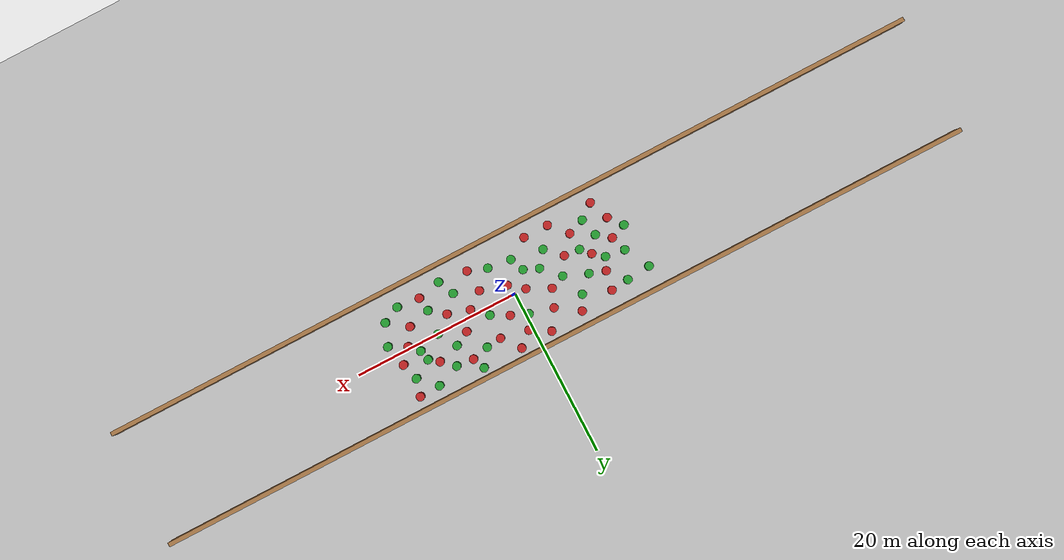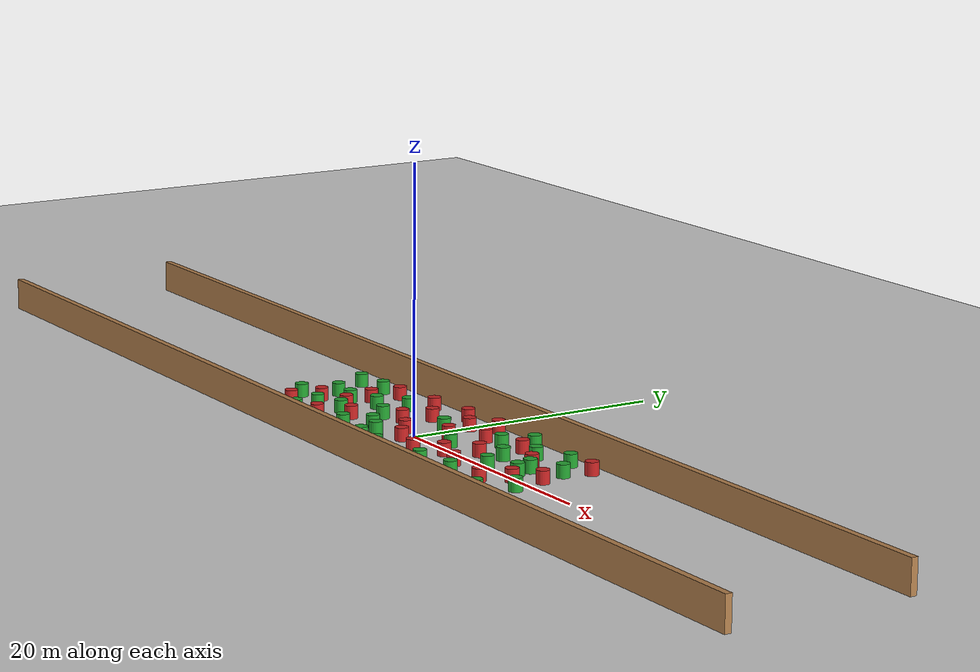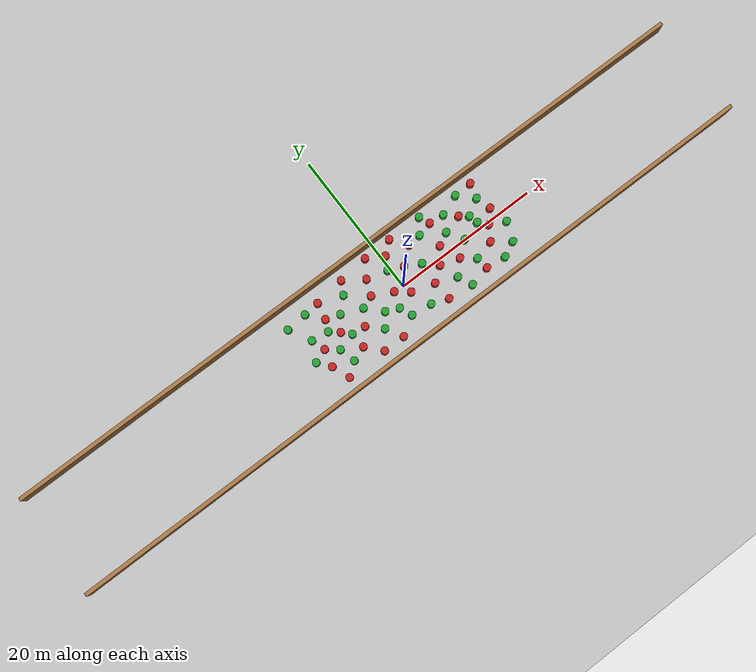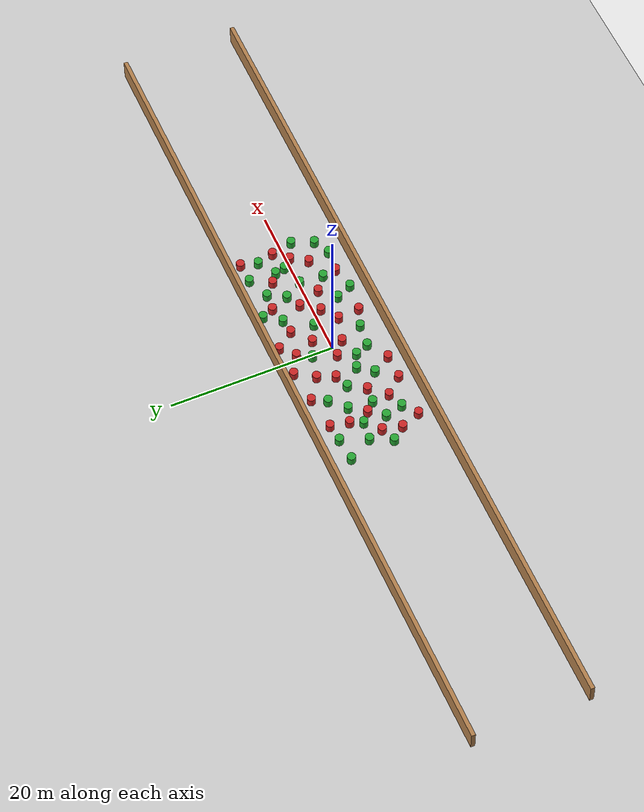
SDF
<sdf version="1.7">
 <world name="default">
  <light name="sun" type="directional">
   <pose>0 0 10 0 -0 0</pose>
   <diffuse>0.8 0.8 0.8 1</diffuse>
   <specular>0.2 0.2 0.2 1</specular>
   <attenuation>
    <range>1000</range>
    <constant>0.9</constant>
    <linear>0.01</linear>
    <quadratic>0.001</quadratic>
   </attenuation>
   <direction>-0.5 0.1 -0.9</direction>
   <spot><inner_angle>0</inner_angle><outer_angle>0</outer_angle><falloff>0</falloff></spot>
  </light>
  <model name="ground_plane">
   <static>1</static>
   <link name="link">
    <collision name="collision">
     <geometry><plane><normal>0 0 1</normal><size>100 100</size></plane></geometry>
     <surface>
      <contact><collide_bitmask>65535</collide_bitmask></contact>
      <friction><ode><mu>100</mu><mu2>50</mu2></ode></friction>
     </surface>
    </collision>
    <visual name="visual">
     <cast_shadows>0</cast_shadows>
     <geometry><plane><normal>0 0 1</normal><size>100 100</size></plane></geometry>
     <material>
      <script><uri>file://media/materials/scripts/gazebo.material</uri><name>Gazebo/Grey</name></script>
     </material>
    </visual>
   </link>
  </model>
  <gravity>0 0 -9.8</gravity>
  <magnetic_field>6e-06 2.3e-05 -4.2e-05</magnetic_field>
  <atmosphere type="adiabatic"/>
  <physics type="ode">
   <max_step_size>0.001</max_step_size>
   <real_time_factor>1</real_time_factor>
   <real_time_update_rate>1000</real_time_update_rate>
  </physics>
  <scene><ambient>0.4 0.4 0.4 1</ambient><background>0.7 0.7 0.7 1</background><shadows>1</shadows></scene>
  <spherical_coordinates>
   <surface_model>EARTH_WGS84</surface_model>
   <latitude_deg>0</latitude_deg>
   <longitude_deg>0</longitude_deg>
   <elevation>0</elevation>
   <heading_deg>0</heading_deg>
  </spherical_coordinates>
  <model name="Astar_Dij_test.world">
   <pose>-2.78716 -0.074871 0 0 -0 0</pose>
   <link name="Wall_0">
    <collision name="Wall_0_Collision">
     <geometry><box><size>100 0.5 2.5</size></box></geometry>
     <pose>0 0 1.25 0 -0 0</pose>
    </collision>
    <visual name="Wall_0_Visual">
     <pose>0 0 1.25 0 -0 0</pose>
     <geometry><box><size>100 0.5 2.5</size></box></geometry>
     <material>
      <script><uri>file://media/materials/scripts/gazebo.material</uri><name>Gazebo/Wood</name></script>
      <ambient>1 1 1 1</ambient>
     </material>
     <meta><layer>0</layer></meta>
    </visual>
    <pose>0.008254 6.97038 0 0 -0 0</pose>
   </link>
   <link name="Wall_2">
    <collision name="Wall_2_Collision">
     <geometry><box><size>100 0.5 2.5</size></box></geometry>
     <pose>0 0 1.25 0 -0 0</pose>
    </collision>
    <visual name="Wall_2_Visual">
     <pose>0 0 1.25 0 -0 0</pose>
     <geometry><box><size>100 0.5 2.5</size></box></geometry>
     <material>
      <script><uri>file://media/materials/scripts/gazebo.material</uri><name>Gazebo/Wood</name></script>
      <ambient>1 1 1 1</ambient>
     </material>
     <meta><layer>0</layer></meta>
    </visual>
    <pose>-0.008254 -6.97038 0 0 -0 0</pose>
   </link>
   <static>1</static>
  </model>
  <model name="Astar_Dij_test.world_0">
   <link name="link">
    <inertial>
     <mass>20</mass>
     <inertia><ixx>2.91667</ixx><ixy>0</ixy><ixz>0</ixz><iyy>2.91667</iyy><iyz>0</iyz><izz>2.5</izz></inertia>
    </inertial>
    <visual name="visual">
     <geometry><cylinder><radius>0.5</radius><length>1</length></cylinder></geometry>
     <material>
      <script><name>Gazebo/Green</name><uri>file://media/materials/scripts/gazebo.material</uri></script>
      <shader type="pixel"><normal_map>__default__</normal_map></shader>
      <ambient>0 1 0 1</ambient>
      <diffuse>0 1 0 1</diffuse>
      <specular>0.1 0.1 0.1 1</specular>
      <emissive>0 0 0 1</emissive>
     </material>
    </visual>
    <collision name="collision">
     <geometry><cylinder><radius>0.5</radius><length>1</length></cylinder></geometry>
     <surface>
      <friction>
       <ode><mu>1</mu><mu2>1</mu2><fdir1>0 0 0</fdir1><slip1>0</slip1><slip2>0</slip2></ode>
       <torsional>
        <coefficient>1</coefficient>
        <patch_radius>0</patch_radius>
        <surface_radius>0</surface_radius>
        <use_patch_radius>1</use_patch_radius>
        <ode><slip>0</slip></ode>
       </torsional>
      </friction>
      <bounce><restitution_coefficient>0</restitution_coefficient><threshold>1e+06</threshold></bounce>
      <contact>
       <collide_without_contact>0</collide_without_contact>
       <collide_without_contact_bitmask>1</collide_without_contact_bitmask>
       <collide_bitmask>1</collide_bitmask>
       <ode>
        <soft_cfm>0</soft_cfm>
        <soft_erp>0.2</soft_erp>
        <kp>1e+13</kp>
        <kd>1</kd>
        <max_vel>0.01</max_vel>
        <min_depth>0</min_depth>
       </ode>
       <bullet>
        <split_impulse>1</split_impulse>
        <split_impulse_penetration_threshold>-0.01</split_impulse_penetration_threshold>
        <soft_cfm>0</soft_cfm>
        <soft_erp>0.2</soft_erp>
        <kp>1e+13</kp>
        <kd>1</kd>
       </bullet>
      </contact>
     </surface>
    </collision>
   </link>
   <link name="link_0">
    <inertial>
     <mass>20</mass>
     <inertia><ixx>2.91667</ixx><ixy>0</ixy><ixz>0</ixz><iyy>2.91667</iyy><iyz>0</iyz><izz>2.5</izz></inertia>
    </inertial>
    <pose>3.54109 -0.119892 0 0 -0 0</pose>
    <visual name="visual">
     <geometry><cylinder><radius>0.5</radius><length>1</length></cylinder></geometry>
     <material>
      <lighting>1</lighting>
      <script><uri>file://media/materials/scripts/gazebo.material</uri><name>Gazebo/Red</name></script>
      <shader type="pixel"><normal_map>__default__</normal_map></shader>
      <ambient>1 0 0 1</ambient>
      <diffuse>1 0 0 1</diffuse>
      <specular>0.1 0.1 0.1 1</specular>
      <emissive>0 0 0 1</emissive>
     </material>
    </visual>
    <collision name="collision">
     <geometry><cylinder><radius>0.5</radius><length>1</length></cylinder></geometry>
     <surface>
      <friction>
       <ode><mu>1</mu><mu2>1</mu2><fdir1>0 0 0</fdir1><slip1>0</slip1><slip2>0</slip2></ode>
       <torsional>
        <coefficient>1</coefficient>
        <patch_radius>0</patch_radius>
        <surface_radius>0</surface_radius>
        <use_patch_radius>1</use_patch_radius>
        <ode><slip>0</slip></ode>
       </torsional>
      </friction>
      <bounce><restitution_coefficient>0</restitution_coefficient><threshold>1e+06</threshold></bounce>
      <contact>
       <collide_without_contact>0</collide_without_contact>
       <collide_without_contact_bitmask>1</collide_without_contact_bitmask>
       <collide_bitmask>1</collide_bitmask>
       <ode>
        <soft_cfm>0</soft_cfm>
        <soft_erp>0.2</soft_erp>
        <kp>1e+13</kp>
        <kd>1</kd>
        <max_vel>0.01</max_vel>
        <min_depth>0</min_depth>
       </ode>
       <bullet>
        <split_impulse>1</split_impulse>
        <split_impulse_penetration_threshold>-0.01</split_impulse_penetration_threshold>
        <soft_cfm>0</soft_cfm>
        <soft_erp>0.2</soft_erp>
        <kp>1e+13</kp>
        <kd>1</kd>
       </bullet>
      </contact>
     </surface>
    </collision>
   </link>
   <link name="link_0_clone">
    <inertial>
     <mass>20</mass>
     <inertia><ixx>2.91667</ixx><ixy>0</ixy><ixz>0</ixz><iyy>2.91667</iyy><iyz>0</iyz><izz>2.5</izz></inertia>
    </inertial>
    <pose>5.36627 -3.50187 0 0 -0 0</pose>
    <visual name="visual">
     <geometry><cylinder><radius>0.5</radius><length>1</length></cylinder></geometry>
     <material>
      <lighting>1</lighting>
      <script><uri>file://media/materials/scripts/gazebo.material</uri><name>Gazebo/Red</name></script>
      <shader type="pixel"><normal_map>__default__</normal_map></shader>
      <ambient>1 0 0 1</ambient>
      <diffuse>1 0 0 1</diffuse>
      <specular>0.1 0.1 0.1 1</specular>
      <emissive>0 0 0 1</emissive>
     </material>
    </visual>
    <collision name="collision">
     <geometry><cylinder><radius>0.5</radius><length>1</length></cylinder></geometry>
     <surface>
      <friction>
       <ode><mu>1</mu><mu2>1</mu2><fdir1>0 0 0</fdir1><slip1>0</slip1><slip2>0</slip2></ode>
       <torsional>
        <coefficient>1</coefficient>
        <patch_radius>0</patch_radius>
        <surface_radius>0</surface_radius>
        <use_patch_radius>1</use_patch_radius>
        <ode><slip>0</slip></ode>
       </torsional>
      </friction>
      <bounce><restitution_coefficient>0</restitution_coefficient><threshold>1e+06</threshold></bounce>
      <contact>
       <collide_without_contact>0</collide_without_contact>
       <collide_without_contact_bitmask>1</collide_without_contact_bitmask>
       <collide_bitmask>1</collide_bitmask>
       <ode>
        <soft_cfm>0</soft_cfm>
        <soft_erp>0.2</soft_erp>
        <kp>1e+13</kp>
        <kd>1</kd>
        <max_vel>0.01</max_vel>
        <min_depth>0</min_depth>
       </ode>
       <bullet>
        <split_impulse>1</split_impulse>
        <split_impulse_penetration_threshold>-0.01</split_impulse_penetration_threshold>
        <soft_cfm>0</soft_cfm>
        <soft_erp>0.2</soft_erp>
        <kp>1e+13</kp>
        <kd>1</kd>
       </bullet>
      </contact>
     </surface>
    </collision>
   </link>
   <link name="link_0_clone_0">
    <inertial>
     <mass>20</mass>
     <inertia><ixx>2.91667</ixx><ixy>0</ixy><ixz>0</ixz><iyy>2.91667</iyy><iyz>0</iyz><izz>2.5</izz></inertia>
    </inertial>
    <pose>7.05149 -4.8226 0 0 -0 0</pose>
    <visual name="visual">
     <geometry><cylinder><radius>0.5</radius><length>1</length></cylinder></geometry>
     <material>
      <lighting>1</lighting>
      <script><uri>file://media/materials/scripts/gazebo.material</uri><name>Gazebo/Red</name></script>
      <shader type="pixel"><normal_map>__default__</normal_map></shader>
      <ambient>1 0 0 1</ambient>
      <diffuse>1 0 0 1</diffuse>
      <specular>0.1 0.1 0.1 1</specular>
      <emissive>0 0 0 1</emissive>
     </material>
    </visual>
    <collision name="collision">
     <geometry><cylinder><radius>0.5</radius><length>1</length></cylinder></geometry>
     <surface>
      <friction>
       <ode><mu>1</mu><mu2>1</mu2><fdir1>0 0 0</fdir1><slip1>0</slip1><slip2>0</slip2></ode>
       <torsional>
        <coefficient>1</coefficient>
        <patch_radius>0</patch_radius>
        <surface_radius>0</surface_radius>
        <use_patch_radius>1</use_patch_radius>
        <ode><slip>0</slip></ode>
       </torsional>
      </friction>
      <bounce><restitution_coefficient>0</restitution_coefficient><threshold>1e+06</threshold></bounce>
      <contact>
       <collide_without_contact>0</collide_without_contact>
       <collide_without_contact_bitmask>1</collide_without_contact_bitmask>
       <collide_bitmask>1</collide_bitmask>
       <ode>
        <soft_cfm>0</soft_cfm>
        <soft_erp>0.2</soft_erp>
        <kp>1e+13</kp>
        <kd>1</kd>
        <max_vel>0.01</max_vel>
        <min_depth>0</min_depth>
       </ode>
       <bullet>
        <split_impulse>1</split_impulse>
        <split_impulse_penetration_threshold>-0.01</split_impulse_penetration_threshold>
        <soft_cfm>0</soft_cfm>
        <soft_erp>0.2</soft_erp>
        <kp>1e+13</kp>
        <kd>1</kd>
       </bullet>
      </contact>
     </surface>
    </collision>
   </link>
   <link name="link_0_clone_1">
    <inertial>
     <mass>20</mass>
     <inertia><ixx>2.91667</ixx><ixy>0</ixy><ixz>0</ixz><iyy>2.91667</iyy><iyz>0</iyz><izz>2.5</izz></inertia>
    </inertial>
    <pose>8.3259 -1.65884 0 0 -0 0</pose>
    <visual name="visual">
     <geometry><cylinder><radius>0.5</radius><length>1</length></cylinder></geometry>
     <material>
      <lighting>1</lighting>
      <script><uri>file://media/materials/scripts/gazebo.material</uri><name>Gazebo/Red</name></script>
      <shader type="pixel"><normal_map>__default__</normal_map></shader>
      <ambient>1 0 0 1</ambient>
      <diffuse>1 0 0 1</diffuse>
      <specular>0.1 0.1 0.1 1</specular>
      <emissive>0 0 0 1</emissive>
     </material>
    </visual>
    <collision name="collision">
     <geometry><cylinder><radius>0.5</radius><length>1</length></cylinder></geometry>
     <surface>
      <friction>
       <ode><mu>1</mu><mu2>1</mu2><fdir1>0 0 0</fdir1><slip1>0</slip1><slip2>0</slip2></ode>
       <torsional>
        <coefficient>1</coefficient>
        <patch_radius>0</patch_radius>
        <surface_radius>0</surface_radius>
        <use_patch_radius>1</use_patch_radius>
        <ode><slip>0</slip></ode>
       </torsional>
      </friction>
      <bounce><restitution_coefficient>0</restitution_coefficient><threshold>1e+06</threshold></bounce>
      <contact>
       <collide_without_contact>0</collide_without_contact>
       <collide_without_contact_bitmask>1</collide_without_contact_bitmask>
       <collide_bitmask>1</collide_bitmask>
       <ode>
        <soft_cfm>0</soft_cfm>
        <soft_erp>0.2</soft_erp>
        <kp>1e+13</kp>
        <kd>1</kd>
        <max_vel>0.01</max_vel>
        <min_depth>0</min_depth>
       </ode>
       <bullet>
        <split_impulse>1</split_impulse>
        <split_impulse_penetration_threshold>-0.01</split_impulse_penetration_threshold>
        <soft_cfm>0</soft_cfm>
        <soft_erp>0.2</soft_erp>
        <kp>1e+13</kp>
        <kd>1</kd>
       </bullet>
      </contact>
     </surface>
    </collision>
   </link>
   <link name="link_0_clone_10">
    <inertial>
     <mass>20</mass>
     <inertia><ixx>2.91667</ixx><ixy>0</ixy><ixz>0</ixz><iyy>2.91667</iyy><iyz>0</iyz><izz>2.5</izz></inertia>
    </inertial>
    <pose>12.0197 -4.31509 0 0 -0 0</pose>
    <visual name="visual">
     <geometry><cylinder><radius>0.5</radius><length>1</length></cylinder></geometry>
     <material>
      <lighting>1</lighting>
      <script><uri>file://media/materials/scripts/gazebo.material</uri><name>Gazebo/Red</name></script>
      <shader type="pixel"><normal_map>__default__</normal_map></shader>
      <ambient>1 0 0 1</ambient>
      <diffuse>1 0 0 1</diffuse>
      <specular>0.1 0.1 0.1 1</specular>
      <emissive>0 0 0 1</emissive>
     </material>
    </visual>
    <collision name="collision">
     <geometry><cylinder><radius>0.5</radius><length>1</length></cylinder></geometry>
     <surface>
      <friction>
       <ode><mu>1</mu><mu2>1</mu2><fdir1>0 0 0</fdir1><slip1>0</slip1><slip2>0</slip2></ode>
       <torsional>
        <coefficient>1</coefficient>
        <patch_radius>0</patch_radius>
        <surface_radius>0</surface_radius>
        <use_patch_radius>1</use_patch_radius>
        <ode><slip>0</slip></ode>
       </torsional>
      </friction>
      <bounce><restitution_coefficient>0</restitution_coefficient><threshold>1e+06</threshold></bounce>
      <contact>
       <collide_without_contact>0</collide_without_contact>
       <collide_without_contact_bitmask>1</collide_without_contact_bitmask>
       <collide_bitmask>1</collide_bitmask>
       <ode>
        <soft_cfm>0</soft_cfm>
        <soft_erp>0.2</soft_erp>
        <kp>1e+13</kp>
        <kd>1</kd>
        <max_vel>0.01</max_vel>
        <min_depth>0</min_depth>
       </ode>
       <bullet>
        <split_impulse>1</split_impulse>
        <split_impulse_penetration_threshold>-0.01</split_impulse_penetration_threshold>
        <soft_cfm>0</soft_cfm>
        <soft_erp>0.2</soft_erp>
        <kp>1e+13</kp>
        <kd>1</kd>
       </bullet>
      </contact>
     </surface>
    </collision>
   </link>
   <link name="link_0_clone_11">
    <inertial>
     <mass>20</mass>
     <inertia><ixx>2.91667</ixx><ixy>0</ixy><ixz>0</ixz><iyy>2.91667</iyy><iyz>0</iyz><izz>2.5</izz></inertia>
    </inertial>
    <pose>-0.214613 -4.8039 -0 0 -0 0</pose>
    <visual name="visual">
     <geometry><cylinder><radius>0.5</radius><length>1</length></cylinder></geometry>
     <material>
      <lighting>1</lighting>
      <script><uri>file://media/materials/scripts/gazebo.material</uri><name>Gazebo/Red</name></script>
      <shader type="pixel"><normal_map>__default__</normal_map></shader>
      <ambient>1 0 0 1</ambient>
      <diffuse>1 0 0 1</diffuse>
      <specular>0.1 0.1 0.1 1</specular>
      <emissive>0 0 0 1</emissive>
     </material>
    </visual>
    <collision name="collision">
     <geometry><cylinder><radius>0.5</radius><length>1</length></cylinder></geometry>
     <surface>
      <friction>
       <ode><mu>1</mu><mu2>1</mu2><fdir1>0 0 0</fdir1><slip1>0</slip1><slip2>0</slip2></ode>
       <torsional>
        <coefficient>1</coefficient>
        <patch_radius>0</patch_radius>
        <surface_radius>0</surface_radius>
        <use_patch_radius>1</use_patch_radius>
        <ode><slip>0</slip></ode>
       </torsional>
      </friction>
      <bounce><restitution_coefficient>0</restitution_coefficient><threshold>1e+06</threshold></bounce>
      <contact>
       <collide_without_contact>0</collide_without_contact>
       <collide_without_contact_bitmask>1</collide_without_contact_bitmask>
       <collide_bitmask>1</collide_bitmask>
       <ode>
        <soft_cfm>0</soft_cfm>
        <soft_erp>0.2</soft_erp>
        <kp>1e+13</kp>
        <kd>1</kd>
        <max_vel>0.01</max_vel>
        <min_depth>0</min_depth>
       </ode>
       <bullet>
        <split_impulse>1</split_impulse>
        <split_impulse_penetration_threshold>-0.01</split_impulse_penetration_threshold>
        <soft_cfm>0</soft_cfm>
        <soft_erp>0.2</soft_erp>
        <kp>1e+13</kp>
        <kd>1</kd>
       </bullet>
      </contact>
     </surface>
    </collision>
   </link>
   <link name="link_0_clone_12">
    <inertial>
     <mass>20</mass>
     <inertia><ixx>2.91667</ixx><ixy>0</ixy><ixz>0</ixz><iyy>2.91667</iyy><iyz>0</iyz><izz>2.5</izz></inertia>
    </inertial>
    <pose>-3.18161 1.14297 -0 0 -0 0</pose>
    <visual name="visual">
     <geometry><cylinder><radius>0.5</radius><length>1</length></cylinder></geometry>
     <material>
      <lighting>1</lighting>
      <script><uri>file://media/materials/scripts/gazebo.material</uri><name>Gazebo/Red</name></script>
      <shader type="pixel"><normal_map>__default__</normal_map></shader>
      <ambient>1 0 0 1</ambient>
      <diffuse>1 0 0 1</diffuse>
      <specular>0.1 0.1 0.1 1</specular>
      <emissive>0 0 0 1</emissive>
     </material>
    </visual>
    <collision name="collision">
     <geometry><cylinder><radius>0.5</radius><length>1</length></cylinder></geometry>
     <surface>
      <friction>
       <ode><mu>1</mu><mu2>1</mu2><fdir1>0 0 0</fdir1><slip1>0</slip1><slip2>0</slip2></ode>
       <torsional>
        <coefficient>1</coefficient>
        <patch_radius>0</patch_radius>
        <surface_radius>0</surface_radius>
        <use_patch_radius>1</use_patch_radius>
        <ode><slip>0</slip></ode>
       </torsional>
      </friction>
      <bounce><restitution_coefficient>0</restitution_coefficient><threshold>1e+06</threshold></bounce>
      <contact>
       <collide_without_contact>0</collide_without_contact>
       <collide_without_contact_bitmask>1</collide_without_contact_bitmask>
       <collide_bitmask>1</collide_bitmask>
       <ode>
        <soft_cfm>0</soft_cfm>
        <soft_erp>0.2</soft_erp>
        <kp>1e+13</kp>
        <kd>1</kd>
        <max_vel>0.01</max_vel>
        <min_depth>0</min_depth>
       </ode>
       <bullet>
        <split_impulse>1</split_impulse>
        <split_impulse_penetration_threshold>-0.01</split_impulse_penetration_threshold>
        <soft_cfm>0</soft_cfm>
        <soft_erp>0.2</soft_erp>
        <kp>1e+13</kp>
        <kd>1</kd>
       </bullet>
      </contact>
     </surface>
    </collision>
   </link>
   <link name="link_0_clone_13">
    <inertial>
     <mass>20</mass>
     <inertia><ixx>2.91667</ixx><ixy>0</ixy><ixz>0</ixz><iyy>2.91667</iyy><iyz>0</iyz><izz>2.5</izz></inertia>
    </inertial>
    <pose>-3.61961 -1.09717 -0 0 -0 0</pose>
    <visual name="visual">
     <geometry><cylinder><radius>0.5</radius><length>1</length></cylinder></geometry>
     <material>
      <lighting>1</lighting>
      <script><uri>file://media/materials/scripts/gazebo.material</uri><name>Gazebo/Red</name></script>
      <shader type="pixel"><normal_map>__default__</normal_map></shader>
      <ambient>1 0 0 1</ambient>
      <diffuse>1 0 0 1</diffuse>
      <specular>0.1 0.1 0.1 1</specular>
      <emissive>0 0 0 1</emissive>
     </material>
    </visual>
    <collision name="collision">
     <geometry><cylinder><radius>0.5</radius><length>1</length></cylinder></geometry>
     <surface>
      <friction>
       <ode><mu>1</mu><mu2>1</mu2><fdir1>0 0 0</fdir1><slip1>0</slip1><slip2>0</slip2></ode>
       <torsional>
        <coefficient>1</coefficient>
        <patch_radius>0</patch_radius>
        <surface_radius>0</surface_radius>
        <use_patch_radius>1</use_patch_radius>
        <ode><slip>0</slip></ode>
       </torsional>
      </friction>
      <bounce><restitution_coefficient>0</restitution_coefficient><threshold>1e+06</threshold></bounce>
      <contact>
       <collide_without_contact>0</collide_without_contact>
       <collide_without_contact_bitmask>1</collide_without_contact_bitmask>
       <collide_bitmask>1</collide_bitmask>
       <ode>
        <soft_cfm>0</soft_cfm>
        <soft_erp>0.2</soft_erp>
        <kp>1e+13</kp>
        <kd>1</kd>
        <max_vel>0.01</max_vel>
        <min_depth>0</min_depth>
       </ode>
       <bullet>
        <split_impulse>1</split_impulse>
        <split_impulse_penetration_threshold>-0.01</split_impulse_penetration_threshold>
        <soft_cfm>0</soft_cfm>
        <soft_erp>0.2</soft_erp>
        <kp>1e+13</kp>
        <kd>1</kd>
       </bullet>
      </contact>
     </surface>
    </collision>
   </link>
   <link name="link_0_clone_14">
    <inertial>
     <mass>20</mass>
     <inertia><ixx>2.91667</ixx><ixy>0</ixy><ixz>0</ixz><iyy>2.91667</iyy><iyz>0</iyz><izz>2.5</izz></inertia>
    </inertial>
    <pose>2.70846 -2.17544 0 0 -0 0</pose>
    <visual name="visual">
     <geometry><cylinder><radius>0.5</radius><length>1</length></cylinder></geometry>
     <material>
      <lighting>1</lighting>
      <script><uri>file://media/materials/scripts/gazebo.material</uri><name>Gazebo/Red</name></script>
      <shader type="pixel"><normal_map>__default__</normal_map></shader>
      <ambient>1 0 0 1</ambient>
      <diffuse>1 0 0 1</diffuse>
      <specular>0.1 0.1 0.1 1</specular>
      <emissive>0 0 0 1</emissive>
     </material>
    </visual>
    <collision name="collision">
     <geometry><cylinder><radius>0.5</radius><length>1</length></cylinder></geometry>
     <surface>
      <friction>
       <ode><mu>1</mu><mu2>1</mu2><fdir1>0 0 0</fdir1><slip1>0</slip1><slip2>0</slip2></ode>
       <torsional>
        <coefficient>1</coefficient>
        <patch_radius>0</patch_radius>
        <surface_radius>0</surface_radius>
        <use_patch_radius>1</use_patch_radius>
        <ode><slip>0</slip></ode>
       </torsional>
      </friction>
      <bounce><restitution_coefficient>0</restitution_coefficient><threshold>1e+06</threshold></bounce>
      <contact>
       <collide_without_contact>0</collide_without_contact>
       <collide_without_contact_bitmask>1</collide_without_contact_bitmask>
       <collide_bitmask>1</collide_bitmask>
       <ode>
        <soft_cfm>0</soft_cfm>
        <soft_erp>0.2</soft_erp>
        <kp>1e+13</kp>
        <kd>1</kd>
        <max_vel>0.01</max_vel>
        <min_depth>0</min_depth>
       </ode>
       <bullet>
        <split_impulse>1</split_impulse>
        <split_impulse_penetration_threshold>-0.01</split_impulse_penetration_threshold>
        <soft_cfm>0</soft_cfm>
        <soft_erp>0.2</soft_erp>
        <kp>1e+13</kp>
        <kd>1</kd>
       </bullet>
      </contact>
     </surface>
    </collision>
   </link>
   <link name="link_0_clone_15">
    <inertial>
     <mass>20</mass>
     <inertia><ixx>2.91667</ixx><ixy>0</ixy><ixz>0</ixz><iyy>2.91667</iyy><iyz>0</iyz><izz>2.5</izz></inertia>
    </inertial>
    <pose>-1.92437 -6.72603 -0 0 -0 0</pose>
    <visual name="visual">
     <geometry><cylinder><radius>0.5</radius><length>1</length></cylinder></geometry>
     <material>
      <lighting>1</lighting>
      <script><uri>file://media/materials/scripts/gazebo.material</uri><name>Gazebo/Red</name></script>
      <shader type="pixel"><normal_map>__default__</normal_map></shader>
      <ambient>1 0 0 1</ambient>
      <diffuse>1 0 0 1</diffuse>
      <specular>0.1 0.1 0.1 1</specular>
      <emissive>0 0 0 1</emissive>
     </material>
    </visual>
    <collision name="collision">
     <geometry><cylinder><radius>0.5</radius><length>1</length></cylinder></geometry>
     <surface>
      <friction>
       <ode><mu>1</mu><mu2>1</mu2><fdir1>0 0 0</fdir1><slip1>0</slip1><slip2>0</slip2></ode>
       <torsional>
        <coefficient>1</coefficient>
        <patch_radius>0</patch_radius>
        <surface_radius>0</surface_radius>
        <use_patch_radius>1</use_patch_radius>
        <ode><slip>0</slip></ode>
       </torsional>
      </friction>
      <bounce><restitution_coefficient>0</restitution_coefficient><threshold>1e+06</threshold></bounce>
      <contact>
       <collide_without_contact>0</collide_without_contact>
       <collide_without_contact_bitmask>1</collide_without_contact_bitmask>
       <collide_bitmask>1</collide_bitmask>
       <ode>
        <soft_cfm>0</soft_cfm>
        <soft_erp>0.2</soft_erp>
        <kp>1e+13</kp>
        <kd>1</kd>
        <max_vel>0.01</max_vel>
        <min_depth>0</min_depth>
       </ode>
       <bullet>
        <split_impulse>1</split_impulse>
        <split_impulse_penetration_threshold>-0.01</split_impulse_penetration_threshold>
        <soft_cfm>0</soft_cfm>
        <soft_erp>0.2</soft_erp>
        <kp>1e+13</kp>
        <kd>1</kd>
       </bullet>
      </contact>
     </surface>
    </collision>
   </link>
   <link name="link_0_clone_16">
    <inertial>
     <mass>20</mass>
     <inertia><ixx>2.91667</ixx><ixy>0</ixy><ixz>0</ixz><iyy>2.91667</iyy><iyz>0</iyz><izz>2.5</izz></inertia>
    </inertial>
    <pose>-0.102342 -8.72649 -0 0 -0 0</pose>
    <visual name="visual">
     <geometry><cylinder><radius>0.5</radius><length>1</length></cylinder></geometry>
     <material>
      <lighting>1</lighting>
      <script><uri>file://media/materials/scripts/gazebo.material</uri><name>Gazebo/Red</name></script>
      <shader type="pixel"><normal_map>__default__</normal_map></shader>
      <ambient>1 0 0 1</ambient>
      <diffuse>1 0 0 1</diffuse>
      <specular>0.1 0.1 0.1 1</specular>
      <emissive>0 0 0 1</emissive>
     </material>
    </visual>
    <collision name="collision">
     <geometry><cylinder><radius>0.5</radius><length>1</length></cylinder></geometry>
     <surface>
      <friction>
       <ode><mu>1</mu><mu2>1</mu2><fdir1>0 0 0</fdir1><slip1>0</slip1><slip2>0</slip2></ode>
       <torsional>
        <coefficient>1</coefficient>
        <patch_radius>0</patch_radius>
        <surface_radius>0</surface_radius>
        <use_patch_radius>1</use_patch_radius>
        <ode><slip>0</slip></ode>
       </torsional>
      </friction>
      <bounce><restitution_coefficient>0</restitution_coefficient><threshold>1e+06</threshold></bounce>
      <contact>
       <collide_without_contact>0</collide_without_contact>
       <collide_without_contact_bitmask>1</collide_without_contact_bitmask>
       <collide_bitmask>1</collide_bitmask>
       <ode>
        <soft_cfm>0</soft_cfm>
        <soft_erp>0.2</soft_erp>
        <kp>1e+13</kp>
        <kd>1</kd>
        <max_vel>0.01</max_vel>
        <min_depth>0</min_depth>
       </ode>
       <bullet>
        <split_impulse>1</split_impulse>
        <split_impulse_penetration_threshold>-0.01</split_impulse_penetration_threshold>
        <soft_cfm>0</soft_cfm>
        <soft_erp>0.2</soft_erp>
        <kp>1e+13</kp>
        <kd>1</kd>
       </bullet>
      </contact>
     </surface>
    </collision>
   </link>
   <link name="link_0_clone_17">
    <inertial>
     <mass>20</mass>
     <inertia><ixx>2.91667</ixx><ixy>0</ixy><ixz>0</ixz><iyy>2.91667</iyy><iyz>0</iyz><izz>2.5</izz></inertia>
    </inertial>
    <pose>2.87315 -8.73364 0 0 -0 0</pose>
    <visual name="visual">
     <geometry><cylinder><radius>0.5</radius><length>1</length></cylinder></geometry>
     <material>
      <lighting>1</lighting>
      <script><uri>file://media/materials/scripts/gazebo.material</uri><name>Gazebo/Red</name></script>
      <shader type="pixel"><normal_map>__default__</normal_map></shader>
      <ambient>1 0 0 1</ambient>
      <diffuse>1 0 0 1</diffuse>
      <specular>0.1 0.1 0.1 1</specular>
      <emissive>0 0 0 1</emissive>
     </material>
    </visual>
    <collision name="collision">
     <geometry><cylinder><radius>0.5</radius><length>1</length></cylinder></geometry>
     <surface>
      <friction>
       <ode><mu>1</mu><mu2>1</mu2><fdir1>0 0 0</fdir1><slip1>0</slip1><slip2>0</slip2></ode>
       <torsional>
        <coefficient>1</coefficient>
        <patch_radius>0</patch_radius>
        <surface_radius>0</surface_radius>
        <use_patch_radius>1</use_patch_radius>
        <ode><slip>0</slip></ode>
       </torsional>
      </friction>
      <bounce><restitution_coefficient>0</restitution_coefficient><threshold>1e+06</threshold></bounce>
      <contact>
       <collide_without_contact>0</collide_without_contact>
       <collide_without_contact_bitmask>1</collide_without_contact_bitmask>
       <collide_bitmask>1</collide_bitmask>
       <ode>
        <soft_cfm>0</soft_cfm>
        <soft_erp>0.2</soft_erp>
        <kp>1e+13</kp>
        <kd>1</kd>
        <max_vel>0.01</max_vel>
        <min_depth>0</min_depth>
       </ode>
       <bullet>
        <split_impulse>1</split_impulse>
        <split_impulse_penetration_threshold>-0.01</split_impulse_penetration_threshold>
        <soft_cfm>0</soft_cfm>
        <soft_erp>0.2</soft_erp>
        <kp>1e+13</kp>
        <kd>1</kd>
       </bullet>
      </contact>
     </surface>
    </collision>
   </link>
   <link name="link_0_clone_18">
    <inertial>
     <mass>20</mass>
     <inertia><ixx>2.91667</ixx><ixy>0</ixy><ixz>0</ixz><iyy>2.91667</iyy><iyz>0</iyz><izz>2.5</izz></inertia>
    </inertial>
    <pose>0.891314 1.68067 0 0 -0 0</pose>
    <visual name="visual">
     <geometry><cylinder><radius>0.5</radius><length>1</length></cylinder></geometry>
     <material>
      <lighting>1</lighting>
      <script><uri>file://media/materials/scripts/gazebo.material</uri><name>Gazebo/Red</name></script>
      <shader type="pixel"><normal_map>__default__</normal_map></shader>
      <ambient>1 0 0 1</ambient>
      <diffuse>1 0 0 1</diffuse>
      <specular>0.1 0.1 0.1 1</specular>
      <emissive>0 0 0 1</emissive>
     </material>
    </visual>
    <collision name="collision">
     <geometry><cylinder><radius>0.5</radius><length>1</length></cylinder></geometry>
     <surface>
      <friction>
       <ode><mu>1</mu><mu2>1</mu2><fdir1>0 0 0</fdir1><slip1>0</slip1><slip2>0</slip2></ode>
       <torsional>
        <coefficient>1</coefficient>
        <patch_radius>0</patch_radius>
        <surface_radius>0</surface_radius>
        <use_patch_radius>1</use_patch_radius>
        <ode><slip>0</slip></ode>
       </torsional>
      </friction>
      <bounce><restitution_coefficient>0</restitution_coefficient><threshold>1e+06</threshold></bounce>
      <contact>
       <collide_without_contact>0</collide_without_contact>
       <collide_without_contact_bitmask>1</collide_without_contact_bitmask>
       <collide_bitmask>1</collide_bitmask>
       <ode>
        <soft_cfm>0</soft_cfm>
        <soft_erp>0.2</soft_erp>
        <kp>1e+13</kp>
        <kd>1</kd>
        <max_vel>0.01</max_vel>
        <min_depth>0</min_depth>
       </ode>
       <bullet>
        <split_impulse>1</split_impulse>
        <split_impulse_penetration_threshold>-0.01</split_impulse_penetration_threshold>
        <soft_cfm>0</soft_cfm>
        <soft_erp>0.2</soft_erp>
        <kp>1e+13</kp>
        <kd>1</kd>
       </bullet>
      </contact>
     </surface>
    </collision>
   </link>
   <link name="link_0_clone_19">
    <inertial>
     <mass>20</mass>
     <inertia><ixx>2.91667</ixx><ixy>0</ixy><ixz>0</ixz><iyy>2.91667</iyy><iyz>0</iyz><izz>2.5</izz></inertia>
    </inertial>
    <pose>4.98594 2.10137 0 0 -0 0</pose>
    <visual name="visual">
     <geometry><cylinder><radius>0.5</radius><length>1</length></cylinder></geometry>
     <material>
      <lighting>1</lighting>
      <script><uri>file://media/materials/scripts/gazebo.material</uri><name>Gazebo/Red</name></script>
      <shader type="pixel"><normal_map>__default__</normal_map></shader>
      <ambient>1 0 0 1</ambient>
      <diffuse>1 0 0 1</diffuse>
      <specular>0.1 0.1 0.1 1</specular>
      <emissive>0 0 0 1</emissive>
     </material>
    </visual>
    <collision name="collision">
     <geometry><cylinder><radius>0.5</radius><length>1</length></cylinder></geometry>
     <surface>
      <friction>
       <ode><mu>1</mu><mu2>1</mu2><fdir1>0 0 0</fdir1><slip1>0</slip1><slip2>0</slip2></ode>
       <torsional>
        <coefficient>1</coefficient>
        <patch_radius>0</patch_radius>
        <surface_radius>0</surface_radius>
        <use_patch_radius>1</use_patch_radius>
        <ode><slip>0</slip></ode>
       </torsional>
      </friction>
      <bounce><restitution_coefficient>0</restitution_coefficient><threshold>1e+06</threshold></bounce>
      <contact>
       <collide_without_contact>0</collide_without_contact>
       <collide_without_contact_bitmask>1</collide_without_contact_bitmask>
       <collide_bitmask>1</collide_bitmask>
       <ode>
        <soft_cfm>0</soft_cfm>
        <soft_erp>0.2</soft_erp>
        <kp>1e+13</kp>
        <kd>1</kd>
        <max_vel>0.01</max_vel>
        <min_depth>0</min_depth>
       </ode>
       <bullet>
        <split_impulse>1</split_impulse>
        <split_impulse_penetration_threshold>-0.01</split_impulse_penetration_threshold>
        <soft_cfm>0</soft_cfm>
        <soft_erp>0.2</soft_erp>
        <kp>1e+13</kp>
        <kd>1</kd>
       </bullet>
      </contact>
     </surface>
    </collision>
   </link>
   <link name="link_0_clone_2">
    <inertial>
     <mass>20</mass>
     <inertia><ixx>2.91667</ixx><ixy>0</ixy><ixz>0</ixz><iyy>2.91667</iyy><iyz>0</iyz><izz>2.5</izz></inertia>
    </inertial>
    <pose>13.5266 -2.31251 0 0 -0 0</pose>
    <visual name="visual">
     <geometry><cylinder><radius>0.5</radius><length>1</length></cylinder></geometry>
     <material>
      <lighting>1</lighting>
      <script><uri>file://media/materials/scripts/gazebo.material</uri><name>Gazebo/Red</name></script>
      <shader type="pixel"><normal_map>__default__</normal_map></shader>
      <ambient>1 0 0 1</ambient>
      <diffuse>1 0 0 1</diffuse>
      <specular>0.1 0.1 0.1 1</specular>
      <emissive>0 0 0 1</emissive>
     </material>
    </visual>
    <collision name="collision">
     <geometry><cylinder><radius>0.5</radius><length>1</length></cylinder></geometry>
     <surface>
      <friction>
       <ode><mu>1</mu><mu2>1</mu2><fdir1>0 0 0</fdir1><slip1>0</slip1><slip2>0</slip2></ode>
       <torsional>
        <coefficient>1</coefficient>
        <patch_radius>0</patch_radius>
        <surface_radius>0</surface_radius>
        <use_patch_radius>1</use_patch_radius>
        <ode><slip>0</slip></ode>
       </torsional>
      </friction>
      <bounce><restitution_coefficient>0</restitution_coefficient><threshold>1e+06</threshold></bounce>
      <contact>
       <collide_without_contact>0</collide_without_contact>
       <collide_without_contact_bitmask>1</collide_without_contact_bitmask>
       <collide_bitmask>1</collide_bitmask>
       <ode>
        <soft_cfm>0</soft_cfm>
        <soft_erp>0.2</soft_erp>
        <kp>1e+13</kp>
        <kd>1</kd>
        <max_vel>0.01</max_vel>
        <min_depth>0</min_depth>
       </ode>
       <bullet>
        <split_impulse>1</split_impulse>
        <split_impulse_penetration_threshold>-0.01</split_impulse_penetration_threshold>
        <soft_cfm>0</soft_cfm>
        <soft_erp>0.2</soft_erp>
        <kp>1e+13</kp>
        <kd>1</kd>
       </bullet>
      </contact>
     </surface>
    </collision>
   </link>
   <link name="link_0_clone_20">
    <inertial>
     <mass>20</mass>
     <inertia><ixx>2.91667</ixx><ixy>0</ixy><ixz>0</ixz><iyy>2.91667</iyy><iyz>0</iyz><izz>2.5</izz></inertia>
    </inertial>
    <pose>7.23174 0.796534 0 0 -0 0</pose>
    <visual name="visual">
     <geometry><cylinder><radius>0.5</radius><length>1</length></cylinder></geometry>
     <material>
      <lighting>1</lighting>
      <script><uri>file://media/materials/scripts/gazebo.material</uri><name>Gazebo/Red</name></script>
      <shader type="pixel"><normal_map>__default__</normal_map></shader>
      <ambient>1 0 0 1</ambient>
      <diffuse>1 0 0 1</diffuse>
      <specular>0.1 0.1 0.1 1</specular>
      <emissive>0 0 0 1</emissive>
     </material>
    </visual>
    <collision name="collision">
     <geometry><cylinder><radius>0.5</radius><length>1</length></cylinder></geometry>
     <surface>
      <friction>
       <ode><mu>1</mu><mu2>1</mu2><fdir1>0 0 0</fdir1><slip1>0</slip1><slip2>0</slip2></ode>
       <torsional>
        <coefficient>1</coefficient>
        <patch_radius>0</patch_radius>
        <surface_radius>0</surface_radius>
        <use_patch_radius>1</use_patch_radius>
        <ode><slip>0</slip></ode>
       </torsional>
      </friction>
      <bounce><restitution_coefficient>0</restitution_coefficient><threshold>1e+06</threshold></bounce>
      <contact>
       <collide_without_contact>0</collide_without_contact>
       <collide_without_contact_bitmask>1</collide_without_contact_bitmask>
       <collide_bitmask>1</collide_bitmask>
       <ode>
        <soft_cfm>0</soft_cfm>
        <soft_erp>0.2</soft_erp>
        <kp>1e+13</kp>
        <kd>1</kd>
        <max_vel>0.01</max_vel>
        <min_depth>0</min_depth>
       </ode>
       <bullet>
        <split_impulse>1</split_impulse>
        <split_impulse_penetration_threshold>-0.01</split_impulse_penetration_threshold>
        <soft_cfm>0</soft_cfm>
        <soft_erp>0.2</soft_erp>
        <kp>1e+13</kp>
        <kd>1</kd>
       </bullet>
      </contact>
     </surface>
    </collision>
   </link>
   <link name="link_0_clone_21">
    <inertial>
     <mass>20</mass>
     <inertia><ixx>2.91667</ixx><ixy>0</ixy><ixz>0</ixz><iyy>2.91667</iyy><iyz>0</iyz><izz>2.5</izz></inertia>
    </inertial>
    <pose>-5.94782 -4.065 -0 0 -0 0</pose>
    <visual name="visual">
     <geometry><cylinder><radius>0.5</radius><length>1</length></cylinder></geometry>
     <material>
      <lighting>1</lighting>
      <script><uri>file://media/materials/scripts/gazebo.material</uri><name>Gazebo/Red</name></script>
      <shader type="pixel"><normal_map>__default__</normal_map></shader>
      <ambient>1 0 0 1</ambient>
      <diffuse>1 0 0 1</diffuse>
      <specular>0.1 0.1 0.1 1</specular>
      <emissive>0 0 0 1</emissive>
     </material>
    </visual>
    <collision name="collision">
     <geometry><cylinder><radius>0.5</radius><length>1</length></cylinder></geometry>
     <surface>
      <friction>
       <ode><mu>1</mu><mu2>1</mu2><fdir1>0 0 0</fdir1><slip1>0</slip1><slip2>0</slip2></ode>
       <torsional>
        <coefficient>1</coefficient>
        <patch_radius>0</patch_radius>
        <surface_radius>0</surface_radius>
        <use_patch_radius>1</use_patch_radius>
        <ode><slip>0</slip></ode>
       </torsional>
      </friction>
      <bounce><restitution_coefficient>0</restitution_coefficient><threshold>1e+06</threshold></bounce>
      <contact>
       <collide_without_contact>0</collide_without_contact>
       <collide_without_contact_bitmask>1</collide_without_contact_bitmask>
       <collide_bitmask>1</collide_bitmask>
       <ode>
        <soft_cfm>0</soft_cfm>
        <soft_erp>0.2</soft_erp>
        <kp>1e+13</kp>
        <kd>1</kd>
        <max_vel>0.01</max_vel>
        <min_depth>0</min_depth>
       </ode>
       <bullet>
        <split_impulse>1</split_impulse>
        <split_impulse_penetration_threshold>-0.01</split_impulse_penetration_threshold>
        <soft_cfm>0</soft_cfm>
        <soft_erp>0.2</soft_erp>
        <kp>1e+13</kp>
        <kd>1</kd>
       </bullet>
      </contact>
     </surface>
    </collision>
   </link>
   <link name="link_0_clone_22">
    <inertial>
     <mass>20</mass>
     <inertia><ixx>2.91667</ixx><ixy>0</ixy><ixz>0</ixz><iyy>2.91667</iyy><iyz>0</iyz><izz>2.5</izz></inertia>
    </inertial>
    <pose>-3.0687 -3.56629 -0 0 -0 0</pose>
    <visual name="visual">
     <geometry><cylinder><radius>0.5</radius><length>1</length></cylinder></geometry>
     <material>
      <lighting>1</lighting>
      <script><uri>file://media/materials/scripts/gazebo.material</uri><name>Gazebo/Red</name></script>
      <shader type="pixel"><normal_map>__default__</normal_map></shader>
      <ambient>1 0 0 1</ambient>
      <diffuse>1 0 0 1</diffuse>
      <specular>0.1 0.1 0.1 1</specular>
      <emissive>0 0 0 1</emissive>
     </material>
    </visual>
    <collision name="collision">
     <geometry><cylinder><radius>0.5</radius><length>1</length></cylinder></geometry>
     <surface>
      <friction>
       <ode><mu>1</mu><mu2>1</mu2><fdir1>0 0 0</fdir1><slip1>0</slip1><slip2>0</slip2></ode>
       <torsional>
        <coefficient>1</coefficient>
        <patch_radius>0</patch_radius>
        <surface_radius>0</surface_radius>
        <use_patch_radius>1</use_patch_radius>
        <ode><slip>0</slip></ode>
       </torsional>
      </friction>
      <bounce><restitution_coefficient>0</restitution_coefficient><threshold>1e+06</threshold></bounce>
      <contact>
       <collide_without_contact>0</collide_without_contact>
       <collide_without_contact_bitmask>1</collide_without_contact_bitmask>
       <collide_bitmask>1</collide_bitmask>
       <ode>
        <soft_cfm>0</soft_cfm>
        <soft_erp>0.2</soft_erp>
        <kp>1e+13</kp>
        <kd>1</kd>
        <max_vel>0.01</max_vel>
        <min_depth>0</min_depth>
       </ode>
       <bullet>
        <split_impulse>1</split_impulse>
        <split_impulse_penetration_threshold>-0.01</split_impulse_penetration_threshold>
        <soft_cfm>0</soft_cfm>
        <soft_erp>0.2</soft_erp>
        <kp>1e+13</kp>
        <kd>1</kd>
       </bullet>
      </contact>
     </surface>
    </collision>
   </link>
   <link name="link_0_clone_23">
    <inertial>
     <mass>20</mass>
     <inertia><ixx>2.91667</ixx><ixy>0</ixy><ixz>0</ixz><iyy>2.91667</iyy><iyz>0</iyz><izz>2.5</izz></inertia>
    </inertial>
    <pose>-6.49727 -6.36979 -0 0 -0 0</pose>
    <visual name="visual">
     <geometry><cylinder><radius>0.5</radius><length>1</length></cylinder></geometry>
     <material>
      <lighting>1</lighting>
      <script><uri>file://media/materials/scripts/gazebo.material</uri><name>Gazebo/Red</name></script>
      <shader type="pixel"><normal_map>__default__</normal_map></shader>
      <ambient>1 0 0 1</ambient>
      <diffuse>1 0 0 1</diffuse>
      <specular>0.1 0.1 0.1 1</specular>
      <emissive>0 0 0 1</emissive>
     </material>
    </visual>
    <collision name="collision">
     <geometry><cylinder><radius>0.5</radius><length>1</length></cylinder></geometry>
     <surface>
      <friction>
       <ode><mu>1</mu><mu2>1</mu2><fdir1>0 0 0</fdir1><slip1>0</slip1><slip2>0</slip2></ode>
       <torsional>
        <coefficient>1</coefficient>
        <patch_radius>0</patch_radius>
        <surface_radius>0</surface_radius>
        <use_patch_radius>1</use_patch_radius>
        <ode><slip>0</slip></ode>
       </torsional>
      </friction>
      <bounce><restitution_coefficient>0</restitution_coefficient><threshold>1e+06</threshold></bounce>
      <contact>
       <collide_without_contact>0</collide_without_contact>
       <collide_without_contact_bitmask>1</collide_without_contact_bitmask>
       <collide_bitmask>1</collide_bitmask>
       <ode>
        <soft_cfm>0</soft_cfm>
        <soft_erp>0.2</soft_erp>
        <kp>1e+13</kp>
        <kd>1</kd>
        <max_vel>0.01</max_vel>
        <min_depth>0</min_depth>
       </ode>
       <bullet>
        <split_impulse>1</split_impulse>
        <split_impulse_penetration_threshold>-0.01</split_impulse_penetration_threshold>
        <soft_cfm>0</soft_cfm>
        <soft_erp>0.2</soft_erp>
        <kp>1e+13</kp>
        <kd>1</kd>
       </bullet>
      </contact>
     </surface>
    </collision>
   </link>
   <link name="link_0_clone_24">
    <inertial>
     <mass>20</mass>
     <inertia><ixx>2.91667</ixx><ixy>0</ixy><ixz>0</ixz><iyy>2.91667</iyy><iyz>0</iyz><izz>2.5</izz></inertia>
    </inertial>
    <pose>-5.57328 -8.73231 -0 0 -0 0</pose>
    <visual name="visual">
     <geometry><cylinder><radius>0.5</radius><length>1</length></cylinder></geometry>
     <material>
      <lighting>1</lighting>
      <script><uri>file://media/materials/scripts/gazebo.material</uri><name>Gazebo/Red</name></script>
      <shader type="pixel"><normal_map>__default__</normal_map></shader>
      <ambient>1 0 0 1</ambient>
      <diffuse>1 0 0 1</diffuse>
      <specular>0.1 0.1 0.1 1</specular>
      <emissive>0 0 0 1</emissive>
     </material>
    </visual>
    <collision name="collision">
     <geometry><cylinder><radius>0.5</radius><length>1</length></cylinder></geometry>
     <surface>
      <friction>
       <ode><mu>1</mu><mu2>1</mu2><fdir1>0 0 0</fdir1><slip1>0</slip1><slip2>0</slip2></ode>
       <torsional>
        <coefficient>1</coefficient>
        <patch_radius>0</patch_radius>
        <surface_radius>0</surface_radius>
        <use_patch_radius>1</use_patch_radius>
        <ode><slip>0</slip></ode>
       </torsional>
      </friction>
      <bounce><restitution_coefficient>0</restitution_coefficient><threshold>1e+06</threshold></bounce>
      <contact>
       <collide_without_contact>0</collide_without_contact>
       <collide_without_contact_bitmask>1</collide_without_contact_bitmask>
       <collide_bitmask>1</collide_bitmask>
       <ode>
        <soft_cfm>0</soft_cfm>
        <soft_erp>0.2</soft_erp>
        <kp>1e+13</kp>
        <kd>1</kd>
        <max_vel>0.01</max_vel>
        <min_depth>0</min_depth>
       </ode>
       <bullet>
        <split_impulse>1</split_impulse>
        <split_impulse_penetration_threshold>-0.01</split_impulse_penetration_threshold>
        <soft_cfm>0</soft_cfm>
        <soft_erp>0.2</soft_erp>
        <kp>1e+13</kp>
        <kd>1</kd>
       </bullet>
      </contact>
     </surface>
    </collision>
   </link>
   <link name="link_0_clone_25">
    <inertial>
     <mass>20</mass>
     <inertia><ixx>2.91667</ixx><ixy>0</ixy><ixz>0</ixz><iyy>2.91667</iyy><iyz>0</iyz><izz>2.5</izz></inertia>
    </inertial>
    <pose>18.9473 -5.77924 0 0 -0 0</pose>
    <visual name="visual">
     <geometry><cylinder><radius>0.5</radius><length>1</length></cylinder></geometry>
     <material>
      <lighting>1</lighting>
      <script><uri>file://media/materials/scripts/gazebo.material</uri><name>Gazebo/Red</name></script>
      <shader type="pixel"><normal_map>__default__</normal_map></shader>
      <ambient>1 0 0 1</ambient>
      <diffuse>1 0 0 1</diffuse>
      <specular>0.1 0.1 0.1 1</specular>
      <emissive>0 0 0 1</emissive>
     </material>
    </visual>
    <collision name="collision">
     <geometry><cylinder><radius>0.5</radius><length>1</length></cylinder></geometry>
     <surface>
      <friction>
       <ode><mu>1</mu><mu2>1</mu2><fdir1>0 0 0</fdir1><slip1>0</slip1><slip2>0</slip2></ode>
       <torsional>
        <coefficient>1</coefficient>
        <patch_radius>0</patch_radius>
        <surface_radius>0</surface_radius>
        <use_patch_radius>1</use_patch_radius>
        <ode><slip>0</slip></ode>
       </torsional>
      </friction>
      <bounce><restitution_coefficient>0</restitution_coefficient><threshold>1e+06</threshold></bounce>
      <contact>
       <collide_without_contact>0</collide_without_contact>
       <collide_without_contact_bitmask>1</collide_without_contact_bitmask>
       <collide_bitmask>1</collide_bitmask>
       <ode>
        <soft_cfm>0</soft_cfm>
        <soft_erp>0.2</soft_erp>
        <kp>1e+13</kp>
        <kd>1</kd>
        <max_vel>0.01</max_vel>
        <min_depth>0</min_depth>
       </ode>
       <bullet>
        <split_impulse>1</split_impulse>
        <split_impulse_penetration_threshold>-0.01</split_impulse_penetration_threshold>
        <soft_cfm>0</soft_cfm>
        <soft_erp>0.2</soft_erp>
        <kp>1e+13</kp>
        <kd>1</kd>
       </bullet>
      </contact>
     </surface>
    </collision>
   </link>
   <link name="link_0_clone_25_clone">
    <inertial>
     <mass>20</mass>
     <inertia><ixx>2.91667</ixx><ixy>0</ixy><ixz>0</ixz><iyy>2.91667</iyy><iyz>0</iyz><izz>2.5</izz></inertia>
    </inertial>
    <pose>20.1782 -3.87581 0 0 -0 0</pose>
    <visual name="visual">
     <geometry><cylinder><radius>0.5</radius><length>1</length></cylinder></geometry>
     <material>
      <lighting>1</lighting>
      <script><uri>file://media/materials/scripts/gazebo.material</uri><name>Gazebo/Red</name></script>
      <shader type="pixel"><normal_map>__default__</normal_map></shader>
      <ambient>1 0 0 1</ambient>
      <diffuse>1 0 0 1</diffuse>
      <specular>0.1 0.1 0.1 1</specular>
      <emissive>0 0 0 1</emissive>
     </material>
    </visual>
    <collision name="collision">
     <geometry><cylinder><radius>0.5</radius><length>1</length></cylinder></geometry>
     <surface>
      <friction>
       <ode><mu>1</mu><mu2>1</mu2><fdir1>0 0 0</fdir1><slip1>0</slip1><slip2>0</slip2></ode>
       <torsional>
        <coefficient>1</coefficient>
        <patch_radius>0</patch_radius>
        <surface_radius>0</surface_radius>
        <use_patch_radius>1</use_patch_radius>
        <ode><slip>0</slip></ode>
       </torsional>
      </friction>
      <bounce><restitution_coefficient>0</restitution_coefficient><threshold>1e+06</threshold></bounce>
      <contact>
       <collide_without_contact>0</collide_without_contact>
       <collide_without_contact_bitmask>1</collide_without_contact_bitmask>
       <collide_bitmask>1</collide_bitmask>
       <ode>
        <soft_cfm>0</soft_cfm>
        <soft_erp>0.2</soft_erp>
        <kp>1e+13</kp>
        <kd>1</kd>
        <max_vel>0.01</max_vel>
        <min_depth>0</min_depth>
       </ode>
       <bullet>
        <split_impulse>1</split_impulse>
        <split_impulse_penetration_threshold>-0.01</split_impulse_penetration_threshold>
        <soft_cfm>0</soft_cfm>
        <soft_erp>0.2</soft_erp>
        <kp>1e+13</kp>
        <kd>1</kd>
       </bullet>
      </contact>
     </surface>
    </collision>
   </link>
   <link name="link_0_clone_25_clone_0">
    <inertial>
     <mass>20</mass>
     <inertia><ixx>2.91667</ixx><ixy>0</ixy><ixz>0</ixz><iyy>2.91667</iyy><iyz>0</iyz><izz>2.5</izz></inertia>
    </inertial>
    <pose>17.7704 -0.699835 0 0 -0 0</pose>
    <visual name="visual">
     <geometry><cylinder><radius>0.5</radius><length>1</length></cylinder></geometry>
     <material>
      <lighting>1</lighting>
      <script><uri>file://media/materials/scripts/gazebo.material</uri><name>Gazebo/Red</name></script>
      <shader type="pixel"><normal_map>__default__</normal_map></shader>
      <ambient>1 0 0 1</ambient>
      <diffuse>1 0 0 1</diffuse>
      <specular>0.1 0.1 0.1 1</specular>
      <emissive>0 0 0 1</emissive>
     </material>
    </visual>
    <collision name="collision">
     <geometry><cylinder><radius>0.5</radius><length>1</length></cylinder></geometry>
     <surface>
      <friction>
       <ode><mu>1</mu><mu2>1</mu2><fdir1>0 0 0</fdir1><slip1>0</slip1><slip2>0</slip2></ode>
       <torsional>
        <coefficient>1</coefficient>
        <patch_radius>0</patch_radius>
        <surface_radius>0</surface_radius>
        <use_patch_radius>1</use_patch_radius>
        <ode><slip>0</slip></ode>
       </torsional>
      </friction>
      <bounce><restitution_coefficient>0</restitution_coefficient><threshold>1e+06</threshold></bounce>
      <contact>
       <collide_without_contact>0</collide_without_contact>
       <collide_without_contact_bitmask>1</collide_without_contact_bitmask>
       <collide_bitmask>1</collide_bitmask>
       <ode>
        <soft_cfm>0</soft_cfm>
        <soft_erp>0.2</soft_erp>
        <kp>1e+13</kp>
        <kd>1</kd>
        <max_vel>0.01</max_vel>
        <min_depth>0</min_depth>
       </ode>
       <bullet>
        <split_impulse>1</split_impulse>
        <split_impulse_penetration_threshold>-0.01</split_impulse_penetration_threshold>
        <soft_cfm>0</soft_cfm>
        <soft_erp>0.2</soft_erp>
        <kp>1e+13</kp>
        <kd>1</kd>
       </bullet>
      </contact>
     </surface>
    </collision>
   </link>
   <link name="link_0_clone_25_clone_1">
    <inertial>
     <mass>20</mass>
     <inertia><ixx>2.91667</ixx><ixy>0</ixy><ixz>0</ixz><iyy>2.91667</iyy><iyz>0</iyz><izz>2.5</izz></inertia>
    </inertial>
    <pose>21.603 -2.29267 0 0 -0 0</pose>
    <visual name="visual">
     <geometry><cylinder><radius>0.5</radius><length>1</length></cylinder></geometry>
     <material>
      <lighting>1</lighting>
      <script><uri>file://media/materials/scripts/gazebo.material</uri><name>Gazebo/Red</name></script>
      <shader type="pixel"><normal_map>__default__</normal_map></shader>
      <ambient>1 0 0 1</ambient>
      <diffuse>1 0 0 1</diffuse>
      <specular>0.1 0.1 0.1 1</specular>
      <emissive>0 0 0 1</emissive>
     </material>
    </visual>
    <collision name="collision">
     <geometry><cylinder><radius>0.5</radius><length>1</length></cylinder></geometry>
     <surface>
      <friction>
       <ode><mu>1</mu><mu2>1</mu2><fdir1>0 0 0</fdir1><slip1>0</slip1><slip2>0</slip2></ode>
       <torsional>
        <coefficient>1</coefficient>
        <patch_radius>0</patch_radius>
        <surface_radius>0</surface_radius>
        <use_patch_radius>1</use_patch_radius>
        <ode><slip>0</slip></ode>
       </torsional>
      </friction>
      <bounce><restitution_coefficient>0</restitution_coefficient><threshold>1e+06</threshold></bounce>
      <contact>
       <collide_without_contact>0</collide_without_contact>
       <collide_without_contact_bitmask>1</collide_without_contact_bitmask>
       <collide_bitmask>1</collide_bitmask>
       <ode>
        <soft_cfm>0</soft_cfm>
        <soft_erp>0.2</soft_erp>
        <kp>1e+13</kp>
        <kd>1</kd>
        <max_vel>0.01</max_vel>
        <min_depth>0</min_depth>
       </ode>
       <bullet>
        <split_impulse>1</split_impulse>
        <split_impulse_penetration_threshold>-0.01</split_impulse_penetration_threshold>
        <soft_cfm>0</soft_cfm>
        <soft_erp>0.2</soft_erp>
        <kp>1e+13</kp>
        <kd>1</kd>
       </bullet>
      </contact>
     </surface>
    </collision>
   </link>
   <link name="link_0_clone_25_clone_2">
    <inertial>
     <mass>20</mass>
     <inertia><ixx>2.91667</ixx><ixy>0</ixy><ixz>0</ixz><iyy>2.91667</iyy><iyz>0</iyz><izz>2.5</izz></inertia>
    </inertial>
    <pose>21.5702 1.76746 0 0 -0 0</pose>
    <visual name="visual">
     <geometry><cylinder><radius>0.5</radius><length>1</length></cylinder></geometry>
     <material>
      <lighting>1</lighting>
      <script><uri>file://media/materials/scripts/gazebo.material</uri><name>Gazebo/Red</name></script>
      <shader type="pixel"><normal_map>__default__</normal_map></shader>
      <ambient>1 0 0 1</ambient>
      <diffuse>1 0 0 1</diffuse>
      <specular>0.1 0.1 0.1 1</specular>
      <emissive>0 0 0 1</emissive>
     </material>
    </visual>
    <collision name="collision">
     <geometry><cylinder><radius>0.5</radius><length>1</length></cylinder></geometry>
     <surface>
      <friction>
       <ode><mu>1</mu><mu2>1</mu2><fdir1>0 0 0</fdir1><slip1>0</slip1><slip2>0</slip2></ode>
       <torsional>
        <coefficient>1</coefficient>
        <patch_radius>0</patch_radius>
        <surface_radius>0</surface_radius>
        <use_patch_radius>1</use_patch_radius>
        <ode><slip>0</slip></ode>
       </torsional>
      </friction>
      <bounce><restitution_coefficient>0</restitution_coefficient><threshold>1e+06</threshold></bounce>
      <contact>
       <collide_without_contact>0</collide_without_contact>
       <collide_without_contact_bitmask>1</collide_without_contact_bitmask>
       <collide_bitmask>1</collide_bitmask>
       <ode>
        <soft_cfm>0</soft_cfm>
        <soft_erp>0.2</soft_erp>
        <kp>1e+13</kp>
        <kd>1</kd>
        <max_vel>0.01</max_vel>
        <min_depth>0</min_depth>
       </ode>
       <bullet>
        <split_impulse>1</split_impulse>
        <split_impulse_penetration_threshold>-0.01</split_impulse_penetration_threshold>
        <soft_cfm>0</soft_cfm>
        <soft_erp>0.2</soft_erp>
        <kp>1e+13</kp>
        <kd>1</kd>
       </bullet>
      </contact>
     </surface>
    </collision>
   </link>
   <link name="link_0_clone_3">
    <inertial>
     <mass>20</mass>
     <inertia><ixx>2.91667</ixx><ixy>0</ixy><ixz>0</ixz><iyy>2.91667</iyy><iyz>0</iyz><izz>2.5</izz></inertia>
    </inertial>
    <pose>14.2917 0.794786 0 0 -0 0</pose>
    <visual name="visual">
     <geometry><cylinder><radius>0.5</radius><length>1</length></cylinder></geometry>
     <material>
      <lighting>1</lighting>
      <script><uri>file://media/materials/scripts/gazebo.material</uri><name>Gazebo/Red</name></script>
      <shader type="pixel"><normal_map>__default__</normal_map></shader>
      <ambient>1 0 0 1</ambient>
      <diffuse>1 0 0 1</diffuse>
      <specular>0.1 0.1 0.1 1</specular>
      <emissive>0 0 0 1</emissive>
     </material>
    </visual>
    <collision name="collision">
     <geometry><cylinder><radius>0.5</radius><length>1</length></cylinder></geometry>
     <surface>
      <friction>
       <ode><mu>1</mu><mu2>1</mu2><fdir1>0 0 0</fdir1><slip1>0</slip1><slip2>0</slip2></ode>
       <torsional>
        <coefficient>1</coefficient>
        <patch_radius>0</patch_radius>
        <surface_radius>0</surface_radius>
        <use_patch_radius>1</use_patch_radius>
        <ode><slip>0</slip></ode>
       </torsional>
      </friction>
      <bounce><restitution_coefficient>0</restitution_coefficient><threshold>1e+06</threshold></bounce>
      <contact>
       <collide_without_contact>0</collide_without_contact>
       <collide_without_contact_bitmask>1</collide_without_contact_bitmask>
       <collide_bitmask>1</collide_bitmask>
       <ode>
        <soft_cfm>0</soft_cfm>
        <soft_erp>0.2</soft_erp>
        <kp>1e+13</kp>
        <kd>1</kd>
        <max_vel>0.01</max_vel>
        <min_depth>0</min_depth>
       </ode>
       <bullet>
        <split_impulse>1</split_impulse>
        <split_impulse_penetration_threshold>-0.01</split_impulse_penetration_threshold>
        <soft_cfm>0</soft_cfm>
        <soft_erp>0.2</soft_erp>
        <kp>1e+13</kp>
        <kd>1</kd>
       </bullet>
      </contact>
     </surface>
    </collision>
   </link>
   <link name="link_0_clone_4">
    <inertial>
     <mass>20</mass>
     <inertia><ixx>2.91667</ixx><ixy>0</ixy><ixz>0</ixz><iyy>2.91667</iyy><iyz>0</iyz><izz>2.5</izz></inertia>
    </inertial>
    <pose>8.88155 2.22109 0 0 -0 0</pose>
    <visual name="visual">
     <geometry><cylinder><radius>0.5</radius><length>1</length></cylinder></geometry>
     <material>
      <lighting>1</lighting>
      <script><uri>file://media/materials/scripts/gazebo.material</uri><name>Gazebo/Red</name></script>
      <shader type="pixel"><normal_map>__default__</normal_map></shader>
      <ambient>1 0 0 1</ambient>
      <diffuse>1 0 0 1</diffuse>
      <specular>0.1 0.1 0.1 1</specular>
      <emissive>0 0 0 1</emissive>
     </material>
    </visual>
    <collision name="collision">
     <geometry><cylinder><radius>0.5</radius><length>1</length></cylinder></geometry>
     <surface>
      <friction>
       <ode><mu>1</mu><mu2>1</mu2><fdir1>0 0 0</fdir1><slip1>0</slip1><slip2>0</slip2></ode>
       <torsional>
        <coefficient>1</coefficient>
        <patch_radius>0</patch_radius>
        <surface_radius>0</surface_radius>
        <use_patch_radius>1</use_patch_radius>
        <ode><slip>0</slip></ode>
       </torsional>
      </friction>
      <bounce><restitution_coefficient>0</restitution_coefficient><threshold>1e+06</threshold></bounce>
      <contact>
       <collide_without_contact>0</collide_without_contact>
       <collide_without_contact_bitmask>1</collide_without_contact_bitmask>
       <collide_bitmask>1</collide_bitmask>
       <ode>
        <soft_cfm>0</soft_cfm>
        <soft_erp>0.2</soft_erp>
        <kp>1e+13</kp>
        <kd>1</kd>
        <max_vel>0.01</max_vel>
        <min_depth>0</min_depth>
       </ode>
       <bullet>
        <split_impulse>1</split_impulse>
        <split_impulse_penetration_threshold>-0.01</split_impulse_penetration_threshold>
        <soft_cfm>0</soft_cfm>
        <soft_erp>0.2</soft_erp>
        <kp>1e+13</kp>
        <kd>1</kd>
       </bullet>
      </contact>
     </surface>
    </collision>
   </link>
   <link name="link_0_clone_5">
    <inertial>
     <mass>20</mass>
     <inertia><ixx>2.91667</ixx><ixy>0</ixy><ixz>0</ixz><iyy>2.91667</iyy><iyz>0</iyz><izz>2.5</izz></inertia>
    </inertial>
    <pose>10.4978 0.118434 0 0 -0 0</pose>
    <visual name="visual">
     <geometry><cylinder><radius>0.5</radius><length>1</length></cylinder></geometry>
     <material>
      <lighting>1</lighting>
      <script><uri>file://media/materials/scripts/gazebo.material</uri><name>Gazebo/Red</name></script>
      <shader type="pixel"><normal_map>__default__</normal_map></shader>
      <ambient>1 0 0 1</ambient>
      <diffuse>1 0 0 1</diffuse>
      <specular>0.1 0.1 0.1 1</specular>
      <emissive>0 0 0 1</emissive>
     </material>
    </visual>
    <collision name="collision">
     <geometry><cylinder><radius>0.5</radius><length>1</length></cylinder></geometry>
     <surface>
      <friction>
       <ode><mu>1</mu><mu2>1</mu2><fdir1>0 0 0</fdir1><slip1>0</slip1><slip2>0</slip2></ode>
       <torsional>
        <coefficient>1</coefficient>
        <patch_radius>0</patch_radius>
        <surface_radius>0</surface_radius>
        <use_patch_radius>1</use_patch_radius>
        <ode><slip>0</slip></ode>
       </torsional>
      </friction>
      <bounce><restitution_coefficient>0</restitution_coefficient><threshold>1e+06</threshold></bounce>
      <contact>
       <collide_without_contact>0</collide_without_contact>
       <collide_without_contact_bitmask>1</collide_without_contact_bitmask>
       <collide_bitmask>1</collide_bitmask>
       <ode>
        <soft_cfm>0</soft_cfm>
        <soft_erp>0.2</soft_erp>
        <kp>1e+13</kp>
        <kd>1</kd>
        <max_vel>0.01</max_vel>
        <min_depth>0</min_depth>
       </ode>
       <bullet>
        <split_impulse>1</split_impulse>
        <split_impulse_penetration_threshold>-0.01</split_impulse_penetration_threshold>
        <soft_cfm>0</soft_cfm>
        <soft_erp>0.2</soft_erp>
        <kp>1e+13</kp>
        <kd>1</kd>
       </bullet>
      </contact>
     </surface>
    </collision>
   </link>
   <link name="link_0_clone_6">
    <inertial>
     <mass>20</mass>
     <inertia><ixx>2.91667</ixx><ixy>0</ixy><ixz>0</ixz><iyy>2.91667</iyy><iyz>0</iyz><izz>2.5</izz></inertia>
    </inertial>
    <pose>10.1266 -5.74101 0 0 -0 0</pose>
    <visual name="visual">
     <geometry><cylinder><radius>0.5</radius><length>1</length></cylinder></geometry>
     <material>
      <lighting>1</lighting>
      <script><uri>file://media/materials/scripts/gazebo.material</uri><name>Gazebo/Red</name></script>
      <shader type="pixel"><normal_map>__default__</normal_map></shader>
      <ambient>1 0 0 1</ambient>
      <diffuse>1 0 0 1</diffuse>
      <specular>0.1 0.1 0.1 1</specular>
      <emissive>0 0 0 1</emissive>
     </material>
    </visual>
    <collision name="collision">
     <geometry><cylinder><radius>0.5</radius><length>1</length></cylinder></geometry>
     <surface>
      <friction>
       <ode><mu>1</mu><mu2>1</mu2><fdir1>0 0 0</fdir1><slip1>0</slip1><slip2>0</slip2></ode>
       <torsional>
        <coefficient>1</coefficient>
        <patch_radius>0</patch_radius>
        <surface_radius>0</surface_radius>
        <use_patch_radius>1</use_patch_radius>
        <ode><slip>0</slip></ode>
       </torsional>
      </friction>
      <bounce><restitution_coefficient>0</restitution_coefficient><threshold>1e+06</threshold></bounce>
      <contact>
       <collide_without_contact>0</collide_without_contact>
       <collide_without_contact_bitmask>1</collide_without_contact_bitmask>
       <collide_bitmask>1</collide_bitmask>
       <ode>
        <soft_cfm>0</soft_cfm>
        <soft_erp>0.2</soft_erp>
        <kp>1e+13</kp>
        <kd>1</kd>
        <max_vel>0.01</max_vel>
        <min_depth>0</min_depth>
       </ode>
       <bullet>
        <split_impulse>1</split_impulse>
        <split_impulse_penetration_threshold>-0.01</split_impulse_penetration_threshold>
        <soft_cfm>0</soft_cfm>
        <soft_erp>0.2</soft_erp>
        <kp>1e+13</kp>
        <kd>1</kd>
       </bullet>
      </contact>
     </surface>
    </collision>
   </link>
   <link name="link_0_clone_7">
    <inertial>
     <mass>20</mass>
     <inertia><ixx>2.91667</ixx><ixy>0</ixy><ixz>0</ixz><iyy>2.91667</iyy><iyz>0</iyz><izz>2.5</izz></inertia>
    </inertial>
    <pose>10.3373 -8.36463 0 0 -0 0</pose>
    <visual name="visual">
     <geometry><cylinder><radius>0.5</radius><length>1</length></cylinder></geometry>
     <material>
      <lighting>1</lighting>
      <script><uri>file://media/materials/scripts/gazebo.material</uri><name>Gazebo/Red</name></script>
      <shader type="pixel"><normal_map>__default__</normal_map></shader>
      <ambient>1 0 0 1</ambient>
      <diffuse>1 0 0 1</diffuse>
      <specular>0.1 0.1 0.1 1</specular>
      <emissive>0 0 0 1</emissive>
     </material>
    </visual>
    <collision name="collision">
     <geometry><cylinder><radius>0.5</radius><length>1</length></cylinder></geometry>
     <surface>
      <friction>
       <ode><mu>1</mu><mu2>1</mu2><fdir1>0 0 0</fdir1><slip1>0</slip1><slip2>0</slip2></ode>
       <torsional>
        <coefficient>1</coefficient>
        <patch_radius>0</patch_radius>
        <surface_radius>0</surface_radius>
        <use_patch_radius>1</use_patch_radius>
        <ode><slip>0</slip></ode>
       </torsional>
      </friction>
      <bounce><restitution_coefficient>0</restitution_coefficient><threshold>1e+06</threshold></bounce>
      <contact>
       <collide_without_contact>0</collide_without_contact>
       <collide_without_contact_bitmask>1</collide_without_contact_bitmask>
       <collide_bitmask>1</collide_bitmask>
       <ode>
        <soft_cfm>0</soft_cfm>
        <soft_erp>0.2</soft_erp>
        <kp>1e+13</kp>
        <kd>1</kd>
        <max_vel>0.01</max_vel>
        <min_depth>0</min_depth>
       </ode>
       <bullet>
        <split_impulse>1</split_impulse>
        <split_impulse_penetration_threshold>-0.01</split_impulse_penetration_threshold>
        <soft_cfm>0</soft_cfm>
        <soft_erp>0.2</soft_erp>
        <kp>1e+13</kp>
        <kd>1</kd>
       </bullet>
      </contact>
     </surface>
    </collision>
   </link>
   <link name="link_0_clone_8">
    <inertial>
     <mass>20</mass>
     <inertia><ixx>2.91667</ixx><ixy>0</ixy><ixz>0</ixz><iyy>2.91667</iyy><iyz>0</iyz><izz>2.5</izz></inertia>
    </inertial>
    <pose>16.5267 -8.14797 0 0 -0 0</pose>
    <visual name="visual">
     <geometry><cylinder><radius>0.5</radius><length>1</length></cylinder></geometry>
     <material>
      <lighting>1</lighting>
      <script><uri>file://media/materials/scripts/gazebo.material</uri><name>Gazebo/Red</name></script>
      <shader type="pixel"><normal_map>__default__</normal_map></shader>
      <ambient>1 0 0 1</ambient>
      <diffuse>1 0 0 1</diffuse>
      <specular>0.1 0.1 0.1 1</specular>
      <emissive>0 0 0 1</emissive>
     </material>
    </visual>
    <collision name="collision">
     <geometry><cylinder><radius>0.5</radius><length>1</length></cylinder></geometry>
     <surface>
      <friction>
       <ode><mu>1</mu><mu2>1</mu2><fdir1>0 0 0</fdir1><slip1>0</slip1><slip2>0</slip2></ode>
       <torsional>
        <coefficient>1</coefficient>
        <patch_radius>0</patch_radius>
        <surface_radius>0</surface_radius>
        <use_patch_radius>1</use_patch_radius>
        <ode><slip>0</slip></ode>
       </torsional>
      </friction>
      <bounce><restitution_coefficient>0</restitution_coefficient><threshold>1e+06</threshold></bounce>
      <contact>
       <collide_without_contact>0</collide_without_contact>
       <collide_without_contact_bitmask>1</collide_without_contact_bitmask>
       <collide_bitmask>1</collide_bitmask>
       <ode>
        <soft_cfm>0</soft_cfm>
        <soft_erp>0.2</soft_erp>
        <kp>1e+13</kp>
        <kd>1</kd>
        <max_vel>0.01</max_vel>
        <min_depth>0</min_depth>
       </ode>
       <bullet>
        <split_impulse>1</split_impulse>
        <split_impulse_penetration_threshold>-0.01</split_impulse_penetration_threshold>
        <soft_cfm>0</soft_cfm>
        <soft_erp>0.2</soft_erp>
        <kp>1e+13</kp>
        <kd>1</kd>
       </bullet>
      </contact>
     </surface>
    </collision>
   </link>
   <link name="link_0_clone_9">
    <inertial>
     <mass>20</mass>
     <inertia><ixx>2.91667</ixx><ixy>0</ixy><ixz>0</ixz><iyy>2.91667</iyy><iyz>0</iyz><izz>2.5</izz></inertia>
    </inertial>
    <pose>14.588 -5.0993 0 0 -0 0</pose>
    <visual name="visual">
     <geometry><cylinder><radius>0.5</radius><length>1</length></cylinder></geometry>
     <material>
      <lighting>1</lighting>
      <script><uri>file://media/materials/scripts/gazebo.material</uri><name>Gazebo/Red</name></script>
      <shader type="pixel"><normal_map>__default__</normal_map></shader>
      <ambient>1 0 0 1</ambient>
      <diffuse>1 0 0 1</diffuse>
      <specular>0.1 0.1 0.1 1</specular>
      <emissive>0 0 0 1</emissive>
     </material>
    </visual>
    <collision name="collision">
     <geometry><cylinder><radius>0.5</radius><length>1</length></cylinder></geometry>
     <surface>
      <friction>
       <ode><mu>1</mu><mu2>1</mu2><fdir1>0 0 0</fdir1><slip1>0</slip1><slip2>0</slip2></ode>
       <torsional>
        <coefficient>1</coefficient>
        <patch_radius>0</patch_radius>
        <surface_radius>0</surface_radius>
        <use_patch_radius>1</use_patch_radius>
        <ode><slip>0</slip></ode>
       </torsional>
      </friction>
      <bounce><restitution_coefficient>0</restitution_coefficient><threshold>1e+06</threshold></bounce>
      <contact>
       <collide_without_contact>0</collide_without_contact>
       <collide_without_contact_bitmask>1</collide_without_contact_bitmask>
       <collide_bitmask>1</collide_bitmask>
       <ode>
        <soft_cfm>0</soft_cfm>
        <soft_erp>0.2</soft_erp>
        <kp>1e+13</kp>
        <kd>1</kd>
        <max_vel>0.01</max_vel>
        <min_depth>0</min_depth>
       </ode>
       <bullet>
        <split_impulse>1</split_impulse>
        <split_impulse_penetration_threshold>-0.01</split_impulse_penetration_threshold>
        <soft_cfm>0</soft_cfm>
        <soft_erp>0.2</soft_erp>
        <kp>1e+13</kp>
        <kd>1</kd>
       </bullet>
      </contact>
     </surface>
    </collision>
   </link>
   <link name="link_clone">
    <inertial>
     <mass>20</mass>
     <inertia><ixx>2.91667</ixx><ixy>0</ixy><ixz>0</ixz><iyy>2.91667</iyy><iyz>0</iyz><izz>2.5</izz></inertia>
    </inertial>
    <pose>1.01753 -2.83828 0 0 -0 0</pose>
    <visual name="visual">
     <geometry><cylinder><radius>0.5</radius><length>1</length></cylinder></geometry>
     <material>
      <script><name>Gazebo/Green</name><uri>file://media/materials/scripts/gazebo.material</uri></script>
      <shader type="pixel"><normal_map>__default__</normal_map></shader>
      <ambient>0 1 0 1</ambient>
      <diffuse>0 1 0 1</diffuse>
      <specular>0.1 0.1 0.1 1</specular>
      <emissive>0 0 0 1</emissive>
     </material>
    </visual>
    <collision name="collision">
     <geometry><cylinder><radius>0.5</radius><length>1</length></cylinder></geometry>
     <surface>
      <friction>
       <ode><mu>1</mu><mu2>1</mu2><fdir1>0 0 0</fdir1><slip1>0</slip1><slip2>0</slip2></ode>
       <torsional>
        <coefficient>1</coefficient>
        <patch_radius>0</patch_radius>
        <surface_radius>0</surface_radius>
        <use_patch_radius>1</use_patch_radius>
        <ode><slip>0</slip></ode>
       </torsional>
      </friction>
      <bounce><restitution_coefficient>0</restitution_coefficient><threshold>1e+06</threshold></bounce>
      <contact>
       <collide_without_contact>0</collide_without_contact>
       <collide_without_contact_bitmask>1</collide_without_contact_bitmask>
       <collide_bitmask>1</collide_bitmask>
       <ode>
        <soft_cfm>0</soft_cfm>
        <soft_erp>0.2</soft_erp>
        <kp>1e+13</kp>
        <kd>1</kd>
        <max_vel>0.01</max_vel>
        <min_depth>0</min_depth>
       </ode>
       <bullet>
        <split_impulse>1</split_impulse>
        <split_impulse_penetration_threshold>-0.01</split_impulse_penetration_threshold>
        <soft_cfm>0</soft_cfm>
        <soft_erp>0.2</soft_erp>
        <kp>1e+13</kp>
        <kd>1</kd>
       </bullet>
      </contact>
     </surface>
    </collision>
   </link>
   <link name="link_clone_0">
    <inertial>
     <mass>20</mass>
     <inertia><ixx>2.91667</ixx><ixy>0</ixy><ixz>0</ixz><iyy>2.91667</iyy><iyz>0</iyz><izz>2.5</izz></inertia>
    </inertial>
    <pose>1.59827 -6.54346 0 0 -0 0</pose>
    <visual name="visual">
     <geometry><cylinder><radius>0.5</radius><length>1</length></cylinder></geometry>
     <material>
      <script><name>Gazebo/Green</name><uri>file://media/materials/scripts/gazebo.material</uri></script>
      <shader type="pixel"><normal_map>__default__</normal_map></shader>
      <ambient>0 1 0 1</ambient>
      <diffuse>0 1 0 1</diffuse>
      <specular>0.1 0.1 0.1 1</specular>
      <emissive>0 0 0 1</emissive>
     </material>
    </visual>
    <collision name="collision">
     <geometry><cylinder><radius>0.5</radius><length>1</length></cylinder></geometry>
     <surface>
      <friction>
       <ode><mu>1</mu><mu2>1</mu2><fdir1>0 0 0</fdir1><slip1>0</slip1><slip2>0</slip2></ode>
       <torsional>
        <coefficient>1</coefficient>
        <patch_radius>0</patch_radius>
        <surface_radius>0</surface_radius>
        <use_patch_radius>1</use_patch_radius>
        <ode><slip>0</slip></ode>
       </torsional>
      </friction>
      <bounce><restitution_coefficient>0</restitution_coefficient><threshold>1e+06</threshold></bounce>
      <contact>
       <collide_without_contact>0</collide_without_contact>
       <collide_without_contact_bitmask>1</collide_without_contact_bitmask>
       <collide_bitmask>1</collide_bitmask>
       <ode>
        <soft_cfm>0</soft_cfm>
        <soft_erp>0.2</soft_erp>
        <kp>1e+13</kp>
        <kd>1</kd>
        <max_vel>0.01</max_vel>
        <min_depth>0</min_depth>
       </ode>
       <bullet>
        <split_impulse>1</split_impulse>
        <split_impulse_penetration_threshold>-0.01</split_impulse_penetration_threshold>
        <soft_cfm>0</soft_cfm>
        <soft_erp>0.2</soft_erp>
        <kp>1e+13</kp>
        <kd>1</kd>
       </bullet>
      </contact>
     </surface>
    </collision>
   </link>
   <link name="link_clone_1">
    <inertial>
     <mass>20</mass>
     <inertia><ixx>2.91667</ixx><ixy>0</ixy><ixz>0</ixz><iyy>2.91667</iyy><iyz>0</iyz><izz>2.5</izz></inertia>
    </inertial>
    <pose>2.93675 -4.81886 0 0 -0 0</pose>
    <visual name="visual">
     <geometry><cylinder><radius>0.5</radius><length>1</length></cylinder></geometry>
     <material>
      <script><name>Gazebo/Green</name><uri>file://media/materials/scripts/gazebo.material</uri></script>
      <shader type="pixel"><normal_map>__default__</normal_map></shader>
      <ambient>0 1 0 1</ambient>
      <diffuse>0 1 0 1</diffuse>
      <specular>0.1 0.1 0.1 1</specular>
      <emissive>0 0 0 1</emissive>
     </material>
    </visual>
    <collision name="collision">
     <geometry><cylinder><radius>0.5</radius><length>1</length></cylinder></geometry>
     <surface>
      <friction>
       <ode><mu>1</mu><mu2>1</mu2><fdir1>0 0 0</fdir1><slip1>0</slip1><slip2>0</slip2></ode>
       <torsional>
        <coefficient>1</coefficient>
        <patch_radius>0</patch_radius>
        <surface_radius>0</surface_radius>
        <use_patch_radius>1</use_patch_radius>
        <ode><slip>0</slip></ode>
       </torsional>
      </friction>
      <bounce><restitution_coefficient>0</restitution_coefficient><threshold>1e+06</threshold></bounce>
      <contact>
       <collide_without_contact>0</collide_without_contact>
       <collide_without_contact_bitmask>1</collide_without_contact_bitmask>
       <collide_bitmask>1</collide_bitmask>
       <ode>
        <soft_cfm>0</soft_cfm>
        <soft_erp>0.2</soft_erp>
        <kp>1e+13</kp>
        <kd>1</kd>
        <max_vel>0.01</max_vel>
        <min_depth>0</min_depth>
       </ode>
       <bullet>
        <split_impulse>1</split_impulse>
        <split_impulse_penetration_threshold>-0.01</split_impulse_penetration_threshold>
        <soft_cfm>0</soft_cfm>
        <soft_erp>0.2</soft_erp>
        <kp>1e+13</kp>
        <kd>1</kd>
       </bullet>
      </contact>
     </surface>
    </collision>
   </link>
   <link name="link_clone_10">
    <inertial>
     <mass>20</mass>
     <inertia><ixx>2.91667</ixx><ixy>0</ixy><ixz>0</ixz><iyy>2.91667</iyy><iyz>0</iyz><izz>2.5</izz></inertia>
    </inertial>
    <pose>10.3463 -2.74345 0 0 -0 0</pose>
    <visual name="visual">
     <geometry><cylinder><radius>0.5</radius><length>1</length></cylinder></geometry>
     <material>
      <script><name>Gazebo/Green</name><uri>file://media/materials/scripts/gazebo.material</uri></script>
      <shader type="pixel"><normal_map>__default__</normal_map></shader>
      <ambient>0 1 0 1</ambient>
      <diffuse>0 1 0 1</diffuse>
      <specular>0.1 0.1 0.1 1</specular>
      <emissive>0 0 0 1</emissive>
     </material>
    </visual>
    <collision name="collision">
     <geometry><cylinder><radius>0.5</radius><length>1</length></cylinder></geometry>
     <surface>
      <friction>
       <ode><mu>1</mu><mu2>1</mu2><fdir1>0 0 0</fdir1><slip1>0</slip1><slip2>0</slip2></ode>
       <torsional>
        <coefficient>1</coefficient>
        <patch_radius>0</patch_radius>
        <surface_radius>0</surface_radius>
        <use_patch_radius>1</use_patch_radius>
        <ode><slip>0</slip></ode>
       </torsional>
      </friction>
      <bounce><restitution_coefficient>0</restitution_coefficient><threshold>1e+06</threshold></bounce>
      <contact>
       <collide_without_contact>0</collide_without_contact>
       <collide_without_contact_bitmask>1</collide_without_contact_bitmask>
       <collide_bitmask>1</collide_bitmask>
       <ode>
        <soft_cfm>0</soft_cfm>
        <soft_erp>0.2</soft_erp>
        <kp>1e+13</kp>
        <kd>1</kd>
        <max_vel>0.01</max_vel>
        <min_depth>0</min_depth>
       </ode>
       <bullet>
        <split_impulse>1</split_impulse>
        <split_impulse_penetration_threshold>-0.01</split_impulse_penetration_threshold>
        <soft_cfm>0</soft_cfm>
        <soft_erp>0.2</soft_erp>
        <kp>1e+13</kp>
        <kd>1</kd>
       </bullet>
      </contact>
     </surface>
    </collision>
   </link>
   <link name="link_clone_11">
    <inertial>
     <mass>20</mass>
     <inertia><ixx>2.91667</ixx><ixy>0</ixy><ixz>0</ixz><iyy>2.91667</iyy><iyz>0</iyz><izz>2.5</izz></inertia>
    </inertial>
    <pose>8.1048 -7.56167 0 0 -0 0</pose>
    <visual name="visual">
     <geometry><cylinder><radius>0.5</radius><length>1</length></cylinder></geometry>
     <material>
      <script><name>Gazebo/Green</name><uri>file://media/materials/scripts/gazebo.material</uri></script>
      <shader type="pixel"><normal_map>__default__</normal_map></shader>
      <ambient>0 1 0 1</ambient>
      <diffuse>0 1 0 1</diffuse>
      <specular>0.1 0.1 0.1 1</specular>
      <emissive>0 0 0 1</emissive>
     </material>
    </visual>
    <collision name="collision">
     <geometry><cylinder><radius>0.5</radius><length>1</length></cylinder></geometry>
     <surface>
      <friction>
       <ode><mu>1</mu><mu2>1</mu2><fdir1>0 0 0</fdir1><slip1>0</slip1><slip2>0</slip2></ode>
       <torsional>
        <coefficient>1</coefficient>
        <patch_radius>0</patch_radius>
        <surface_radius>0</surface_radius>
        <use_patch_radius>1</use_patch_radius>
        <ode><slip>0</slip></ode>
       </torsional>
      </friction>
      <bounce><restitution_coefficient>0</restitution_coefficient><threshold>1e+06</threshold></bounce>
      <contact>
       <collide_without_contact>0</collide_without_contact>
       <collide_without_contact_bitmask>1</collide_without_contact_bitmask>
       <collide_bitmask>1</collide_bitmask>
       <ode>
        <soft_cfm>0</soft_cfm>
        <soft_erp>0.2</soft_erp>
        <kp>1e+13</kp>
        <kd>1</kd>
        <max_vel>0.01</max_vel>
        <min_depth>0</min_depth>
       </ode>
       <bullet>
        <split_impulse>1</split_impulse>
        <split_impulse_penetration_threshold>-0.01</split_impulse_penetration_threshold>
        <soft_cfm>0</soft_cfm>
        <soft_erp>0.2</soft_erp>
        <kp>1e+13</kp>
        <kd>1</kd>
       </bullet>
      </contact>
     </surface>
    </collision>
   </link>
   <link name="link_clone_12">
    <inertial>
     <mass>20</mass>
     <inertia><ixx>2.91667</ixx><ixy>0</ixy><ixz>0</ixz><iyy>2.91667</iyy><iyz>0</iyz><izz>2.5</izz></inertia>
    </inertial>
    <pose>6.3534 -0.83806 0 0 -0 0</pose>
    <visual name="visual">
     <geometry><cylinder><radius>0.5</radius><length>1</length></cylinder></geometry>
     <material>
      <script><name>Gazebo/Green</name><uri>file://media/materials/scripts/gazebo.material</uri></script>
      <shader type="pixel"><normal_map>__default__</normal_map></shader>
      <ambient>0 1 0 1</ambient>
      <diffuse>0 1 0 1</diffuse>
      <specular>0.1 0.1 0.1 1</specular>
      <emissive>0 0 0 1</emissive>
     </material>
    </visual>
    <collision name="collision">
     <geometry><cylinder><radius>0.5</radius><length>1</length></cylinder></geometry>
     <surface>
      <friction>
       <ode><mu>1</mu><mu2>1</mu2><fdir1>0 0 0</fdir1><slip1>0</slip1><slip2>0</slip2></ode>
       <torsional>
        <coefficient>1</coefficient>
        <patch_radius>0</patch_radius>
        <surface_radius>0</surface_radius>
        <use_patch_radius>1</use_patch_radius>
        <ode><slip>0</slip></ode>
       </torsional>
      </friction>
      <bounce><restitution_coefficient>0</restitution_coefficient><threshold>1e+06</threshold></bounce>
      <contact>
       <collide_without_contact>0</collide_without_contact>
       <collide_without_contact_bitmask>1</collide_without_contact_bitmask>
       <collide_bitmask>1</collide_bitmask>
       <ode>
        <soft_cfm>0</soft_cfm>
        <soft_erp>0.2</soft_erp>
        <kp>1e+13</kp>
        <kd>1</kd>
        <max_vel>0.01</max_vel>
        <min_depth>0</min_depth>
       </ode>
       <bullet>
        <split_impulse>1</split_impulse>
        <split_impulse_penetration_threshold>-0.01</split_impulse_penetration_threshold>
        <soft_cfm>0</soft_cfm>
        <soft_erp>0.2</soft_erp>
        <kp>1e+13</kp>
        <kd>1</kd>
       </bullet>
      </contact>
     </surface>
    </collision>
   </link>
   <link name="link_clone_13">
    <inertial>
     <mass>20</mass>
     <inertia><ixx>2.91667</ixx><ixy>0</ixy><ixz>0</ixz><iyy>2.91667</iyy><iyz>0</iyz><izz>2.5</izz></inertia>
    </inertial>
    <pose>5.34757 -7.21202 0 0 -0 0</pose>
    <visual name="visual">
     <geometry><cylinder><radius>0.5</radius><length>1</length></cylinder></geometry>
     <material>
      <script><name>Gazebo/Green</name><uri>file://media/materials/scripts/gazebo.material</uri></script>
      <shader type="pixel"><normal_map>__default__</normal_map></shader>
      <ambient>0 1 0 1</ambient>
      <diffuse>0 1 0 1</diffuse>
      <specular>0.1 0.1 0.1 1</specular>
      <emissive>0 0 0 1</emissive>
     </material>
    </visual>
    <collision name="collision">
     <geometry><cylinder><radius>0.5</radius><length>1</length></cylinder></geometry>
     <surface>
      <friction>
       <ode><mu>1</mu><mu2>1</mu2><fdir1>0 0 0</fdir1><slip1>0</slip1><slip2>0</slip2></ode>
       <torsional>
        <coefficient>1</coefficient>
        <patch_radius>0</patch_radius>
        <surface_radius>0</surface_radius>
        <use_patch_radius>1</use_patch_radius>
        <ode><slip>0</slip></ode>
       </torsional>
      </friction>
      <bounce><restitution_coefficient>0</restitution_coefficient><threshold>1e+06</threshold></bounce>
      <contact>
       <collide_without_contact>0</collide_without_contact>
       <collide_without_contact_bitmask>1</collide_without_contact_bitmask>
       <collide_bitmask>1</collide_bitmask>
       <ode>
        <soft_cfm>0</soft_cfm>
        <soft_erp>0.2</soft_erp>
        <kp>1e+13</kp>
        <kd>1</kd>
        <max_vel>0.01</max_vel>
        <min_depth>0</min_depth>
       </ode>
       <bullet>
        <split_impulse>1</split_impulse>
        <split_impulse_penetration_threshold>-0.01</split_impulse_penetration_threshold>
        <soft_cfm>0</soft_cfm>
        <soft_erp>0.2</soft_erp>
        <kp>1e+13</kp>
        <kd>1</kd>
       </bullet>
      </contact>
     </surface>
    </collision>
   </link>
   <link name="link_clone_14">
    <inertial>
     <mass>20</mass>
     <inertia><ixx>2.91667</ixx><ixy>0</ixy><ixz>0</ixz><iyy>2.91667</iyy><iyz>0</iyz><izz>2.5</izz></inertia>
    </inertial>
    <pose>-7.78173 -4.75382 -0 0 -0 0</pose>
    <visual name="visual">
     <geometry><cylinder><radius>0.5</radius><length>1</length></cylinder></geometry>
     <material>
      <script><name>Gazebo/Green</name><uri>file://media/materials/scripts/gazebo.material</uri></script>
      <shader type="pixel"><normal_map>__default__</normal_map></shader>
      <ambient>0 1 0 1</ambient>
      <diffuse>0 1 0 1</diffuse>
      <specular>0.1 0.1 0.1 1</specular>
      <emissive>0 0 0 1</emissive>
     </material>
    </visual>
    <collision name="collision">
     <geometry><cylinder><radius>0.5</radius><length>1</length></cylinder></geometry>
     <surface>
      <friction>
       <ode><mu>1</mu><mu2>1</mu2><fdir1>0 0 0</fdir1><slip1>0</slip1><slip2>0</slip2></ode>
       <torsional>
        <coefficient>1</coefficient>
        <patch_radius>0</patch_radius>
        <surface_radius>0</surface_radius>
        <use_patch_radius>1</use_patch_radius>
        <ode><slip>0</slip></ode>
       </torsional>
      </friction>
      <bounce><restitution_coefficient>0</restitution_coefficient><threshold>1e+06</threshold></bounce>
      <contact>
       <collide_without_contact>0</collide_without_contact>
       <collide_without_contact_bitmask>1</collide_without_contact_bitmask>
       <collide_bitmask>1</collide_bitmask>
       <ode>
        <soft_cfm>0</soft_cfm>
        <soft_erp>0.2</soft_erp>
        <kp>1e+13</kp>
        <kd>1</kd>
        <max_vel>0.01</max_vel>
        <min_depth>0</min_depth>
       </ode>
       <bullet>
        <split_impulse>1</split_impulse>
        <split_impulse_penetration_threshold>-0.01</split_impulse_penetration_threshold>
        <soft_cfm>0</soft_cfm>
        <soft_erp>0.2</soft_erp>
        <kp>1e+13</kp>
        <kd>1</kd>
       </bullet>
      </contact>
     </surface>
    </collision>
   </link>
   <link name="link_clone_15">
    <inertial>
     <mass>20</mass>
     <inertia><ixx>2.91667</ixx><ixy>0</ixy><ixz>0</ixz><iyy>2.91667</iyy><iyz>0</iyz><izz>2.5</izz></inertia>
    </inertial>
    <pose>-8.14362 0.678924 -0 0 -0 0</pose>
    <visual name="visual">
     <geometry><cylinder><radius>0.5</radius><length>1</length></cylinder></geometry>
     <material>
      <script><name>Gazebo/Green</name><uri>file://media/materials/scripts/gazebo.material</uri></script>
      <shader type="pixel"><normal_map>__default__</normal_map></shader>
      <ambient>0 1 0 1</ambient>
      <diffuse>0 1 0 1</diffuse>
      <specular>0.1 0.1 0.1 1</specular>
      <emissive>0 0 0 1</emissive>
     </material>
    </visual>
    <collision name="collision">
     <geometry><cylinder><radius>0.5</radius><length>1</length></cylinder></geometry>
     <surface>
      <friction>
       <ode><mu>1</mu><mu2>1</mu2><fdir1>0 0 0</fdir1><slip1>0</slip1><slip2>0</slip2></ode>
       <torsional>
        <coefficient>1</coefficient>
        <patch_radius>0</patch_radius>
        <surface_radius>0</surface_radius>
        <use_patch_radius>1</use_patch_radius>
        <ode><slip>0</slip></ode>
       </torsional>
      </friction>
      <bounce><restitution_coefficient>0</restitution_coefficient><threshold>1e+06</threshold></bounce>
      <contact>
       <collide_without_contact>0</collide_without_contact>
       <collide_without_contact_bitmask>1</collide_without_contact_bitmask>
       <collide_bitmask>1</collide_bitmask>
       <ode>
        <soft_cfm>0</soft_cfm>
        <soft_erp>0.2</soft_erp>
        <kp>1e+13</kp>
        <kd>1</kd>
        <max_vel>0.01</max_vel>
        <min_depth>0</min_depth>
       </ode>
       <bullet>
        <split_impulse>1</split_impulse>
        <split_impulse_penetration_threshold>-0.01</split_impulse_penetration_threshold>
        <soft_cfm>0</soft_cfm>
        <soft_erp>0.2</soft_erp>
        <kp>1e+13</kp>
        <kd>1</kd>
       </bullet>
      </contact>
     </surface>
    </collision>
   </link>
   <link name="link_clone_16">
    <inertial>
     <mass>20</mass>
     <inertia><ixx>2.91667</ixx><ixy>0</ixy><ixz>0</ixz><iyy>2.91667</iyy><iyz>0</iyz><izz>2.5</izz></inertia>
    </inertial>
    <pose>-6.57432 -2.22503 -0 0 -0 0</pose>
    <visual name="visual">
     <geometry><cylinder><radius>0.5</radius><length>1</length></cylinder></geometry>
     <material>
      <script><name>Gazebo/Green</name><uri>file://media/materials/scripts/gazebo.material</uri></script>
      <shader type="pixel"><normal_map>__default__</normal_map></shader>
      <ambient>0 1 0 1</ambient>
      <diffuse>0 1 0 1</diffuse>
      <specular>0.1 0.1 0.1 1</specular>
      <emissive>0 0 0 1</emissive>
     </material>
    </visual>
    <collision name="collision">
     <geometry><cylinder><radius>0.5</radius><length>1</length></cylinder></geometry>
     <surface>
      <friction>
       <ode><mu>1</mu><mu2>1</mu2><fdir1>0 0 0</fdir1><slip1>0</slip1><slip2>0</slip2></ode>
       <torsional>
        <coefficient>1</coefficient>
        <patch_radius>0</patch_radius>
        <surface_radius>0</surface_radius>
        <use_patch_radius>1</use_patch_radius>
        <ode><slip>0</slip></ode>
       </torsional>
      </friction>
      <bounce><restitution_coefficient>0</restitution_coefficient><threshold>1e+06</threshold></bounce>
      <contact>
       <collide_without_contact>0</collide_without_contact>
       <collide_without_contact_bitmask>1</collide_without_contact_bitmask>
       <collide_bitmask>1</collide_bitmask>
       <ode>
        <soft_cfm>0</soft_cfm>
        <soft_erp>0.2</soft_erp>
        <kp>1e+13</kp>
        <kd>1</kd>
        <max_vel>0.01</max_vel>
        <min_depth>0</min_depth>
       </ode>
       <bullet>
        <split_impulse>1</split_impulse>
        <split_impulse_penetration_threshold>-0.01</split_impulse_penetration_threshold>
        <soft_cfm>0</soft_cfm>
        <soft_erp>0.2</soft_erp>
        <kp>1e+13</kp>
        <kd>1</kd>
       </bullet>
      </contact>
     </surface>
    </collision>
   </link>
   <link name="link_clone_17">
    <inertial>
     <mass>20</mass>
     <inertia><ixx>2.91667</ixx><ixy>0</ixy><ixz>0</ixz><iyy>2.91667</iyy><iyz>0</iyz><izz>2.5</izz></inertia>
    </inertial>
    <pose>-5.32485 0.931117 -0 0 -0 0</pose>
    <visual name="visual">
     <geometry><cylinder><radius>0.5</radius><length>1</length></cylinder></geometry>
     <material>
      <script><name>Gazebo/Green</name><uri>file://media/materials/scripts/gazebo.material</uri></script>
      <shader type="pixel"><normal_map>__default__</normal_map></shader>
      <ambient>0 1 0 1</ambient>
      <diffuse>0 1 0 1</diffuse>
      <specular>0.1 0.1 0.1 1</specular>
      <emissive>0 0 0 1</emissive>
     </material>
    </visual>
    <collision name="collision">
     <geometry><cylinder><radius>0.5</radius><length>1</length></cylinder></geometry>
     <surface>
      <friction>
       <ode><mu>1</mu><mu2>1</mu2><fdir1>0 0 0</fdir1><slip1>0</slip1><slip2>0</slip2></ode>
       <torsional>
        <coefficient>1</coefficient>
        <patch_radius>0</patch_radius>
        <surface_radius>0</surface_radius>
        <use_patch_radius>1</use_patch_radius>
        <ode><slip>0</slip></ode>
       </torsional>
      </friction>
      <bounce><restitution_coefficient>0</restitution_coefficient><threshold>1e+06</threshold></bounce>
      <contact>
       <collide_without_contact>0</collide_without_contact>
       <collide_without_contact_bitmask>1</collide_without_contact_bitmask>
       <collide_bitmask>1</collide_bitmask>
       <ode>
        <soft_cfm>0</soft_cfm>
        <soft_erp>0.2</soft_erp>
        <kp>1e+13</kp>
        <kd>1</kd>
        <max_vel>0.01</max_vel>
        <min_depth>0</min_depth>
       </ode>
       <bullet>
        <split_impulse>1</split_impulse>
        <split_impulse_penetration_threshold>-0.01</split_impulse_penetration_threshold>
        <soft_cfm>0</soft_cfm>
        <soft_erp>0.2</soft_erp>
        <kp>1e+13</kp>
        <kd>1</kd>
       </bullet>
      </contact>
     </surface>
    </collision>
   </link>
   <link name="link_clone_18">
    <inertial>
     <mass>20</mass>
     <inertia><ixx>2.91667</ixx><ixy>0</ixy><ixz>0</ixz><iyy>2.91667</iyy><iyz>0</iyz><izz>2.5</izz></inertia>
    </inertial>
    <pose>-4.27642 -2.54771 -0 0 -0 0</pose>
    <visual name="visual">
     <geometry><cylinder><radius>0.5</radius><length>1</length></cylinder></geometry>
     <material>
      <script><name>Gazebo/Green</name><uri>file://media/materials/scripts/gazebo.material</uri></script>
      <shader type="pixel"><normal_map>__default__</normal_map></shader>
      <ambient>0 1 0 1</ambient>
      <diffuse>0 1 0 1</diffuse>
      <specular>0.1 0.1 0.1 1</specular>
      <emissive>0 0 0 1</emissive>
     </material>
    </visual>
    <collision name="collision">
     <geometry><cylinder><radius>0.5</radius><length>1</length></cylinder></geometry>
     <surface>
      <friction>
       <ode><mu>1</mu><mu2>1</mu2><fdir1>0 0 0</fdir1><slip1>0</slip1><slip2>0</slip2></ode>
       <torsional>
        <coefficient>1</coefficient>
        <patch_radius>0</patch_radius>
        <surface_radius>0</surface_radius>
        <use_patch_radius>1</use_patch_radius>
        <ode><slip>0</slip></ode>
       </torsional>
      </friction>
      <bounce><restitution_coefficient>0</restitution_coefficient><threshold>1e+06</threshold></bounce>
      <contact>
       <collide_without_contact>0</collide_without_contact>
       <collide_without_contact_bitmask>1</collide_without_contact_bitmask>
       <collide_bitmask>1</collide_bitmask>
       <ode>
        <soft_cfm>0</soft_cfm>
        <soft_erp>0.2</soft_erp>
        <kp>1e+13</kp>
        <kd>1</kd>
        <max_vel>0.01</max_vel>
        <min_depth>0</min_depth>
       </ode>
       <bullet>
        <split_impulse>1</split_impulse>
        <split_impulse_penetration_threshold>-0.01</split_impulse_penetration_threshold>
        <soft_cfm>0</soft_cfm>
        <soft_erp>0.2</soft_erp>
        <kp>1e+13</kp>
        <kd>1</kd>
       </bullet>
      </contact>
     </surface>
    </collision>
   </link>
   <link name="link_clone_19">
    <inertial>
     <mass>20</mass>
     <inertia><ixx>2.91667</ixx><ixy>0</ixy><ixz>0</ixz><iyy>2.91667</iyy><iyz>0</iyz><izz>2.5</izz></inertia>
    </inertial>
    <pose>-4.41016 -5.276 -0 0 -0 0</pose>
    <visual name="visual">
     <geometry><cylinder><radius>0.5</radius><length>1</length></cylinder></geometry>
     <material>
      <script><name>Gazebo/Green</name><uri>file://media/materials/scripts/gazebo.material</uri></script>
      <shader type="pixel"><normal_map>__default__</normal_map></shader>
      <ambient>0 1 0 1</ambient>
      <diffuse>0 1 0 1</diffuse>
      <specular>0.1 0.1 0.1 1</specular>
      <emissive>0 0 0 1</emissive>
     </material>
    </visual>
    <collision name="collision">
     <geometry><cylinder><radius>0.5</radius><length>1</length></cylinder></geometry>
     <surface>
      <friction>
       <ode><mu>1</mu><mu2>1</mu2><fdir1>0 0 0</fdir1><slip1>0</slip1><slip2>0</slip2></ode>
       <torsional>
        <coefficient>1</coefficient>
        <patch_radius>0</patch_radius>
        <surface_radius>0</surface_radius>
        <use_patch_radius>1</use_patch_radius>
        <ode><slip>0</slip></ode>
       </torsional>
      </friction>
      <bounce><restitution_coefficient>0</restitution_coefficient><threshold>1e+06</threshold></bounce>
      <contact>
       <collide_without_contact>0</collide_without_contact>
       <collide_without_contact_bitmask>1</collide_without_contact_bitmask>
       <collide_bitmask>1</collide_bitmask>
       <ode>
        <soft_cfm>0</soft_cfm>
        <soft_erp>0.2</soft_erp>
        <kp>1e+13</kp>
        <kd>1</kd>
        <max_vel>0.01</max_vel>
        <min_depth>0</min_depth>
       </ode>
       <bullet>
        <split_impulse>1</split_impulse>
        <split_impulse_penetration_threshold>-0.01</split_impulse_penetration_threshold>
        <soft_cfm>0</soft_cfm>
        <soft_erp>0.2</soft_erp>
        <kp>1e+13</kp>
        <kd>1</kd>
       </bullet>
      </contact>
     </surface>
    </collision>
   </link>
   <link name="link_clone_2">
    <inertial>
     <mass>20</mass>
     <inertia><ixx>2.91667</ixx><ixy>0</ixy><ixz>0</ixz><iyy>2.91667</iyy><iyz>0</iyz><izz>2.5</izz></inertia>
    </inertial>
    <pose>-2.05771 -4.6199 -0 0 -0 0</pose>
    <visual name="visual">
     <geometry><cylinder><radius>0.5</radius><length>1</length></cylinder></geometry>
     <material>
      <script><name>Gazebo/Green</name><uri>file://media/materials/scripts/gazebo.material</uri></script>
      <shader type="pixel"><normal_map>__default__</normal_map></shader>
      <ambient>0 1 0 1</ambient>
      <diffuse>0 1 0 1</diffuse>
      <specular>0.1 0.1 0.1 1</specular>
      <emissive>0 0 0 1</emissive>
     </material>
    </visual>
    <collision name="collision">
     <geometry><cylinder><radius>0.5</radius><length>1</length></cylinder></geometry>
     <surface>
      <friction>
       <ode><mu>1</mu><mu2>1</mu2><fdir1>0 0 0</fdir1><slip1>0</slip1><slip2>0</slip2></ode>
       <torsional>
        <coefficient>1</coefficient>
        <patch_radius>0</patch_radius>
        <surface_radius>0</surface_radius>
        <use_patch_radius>1</use_patch_radius>
        <ode><slip>0</slip></ode>
       </torsional>
      </friction>
      <bounce><restitution_coefficient>0</restitution_coefficient><threshold>1e+06</threshold></bounce>
      <contact>
       <collide_without_contact>0</collide_without_contact>
       <collide_without_contact_bitmask>1</collide_without_contact_bitmask>
       <collide_bitmask>1</collide_bitmask>
       <ode>
        <soft_cfm>0</soft_cfm>
        <soft_erp>0.2</soft_erp>
        <kp>1e+13</kp>
        <kd>1</kd>
        <max_vel>0.01</max_vel>
        <min_depth>0</min_depth>
       </ode>
       <bullet>
        <split_impulse>1</split_impulse>
        <split_impulse_penetration_threshold>-0.01</split_impulse_penetration_threshold>
        <soft_cfm>0</soft_cfm>
        <soft_erp>0.2</soft_erp>
        <kp>1e+13</kp>
        <kd>1</kd>
       </bullet>
      </contact>
     </surface>
    </collision>
   </link>
   <link name="link_clone_20">
    <inertial>
     <mass>20</mass>
     <inertia><ixx>2.91667</ixx><ixy>0</ixy><ixz>0</ixz><iyy>2.91667</iyy><iyz>0</iyz><izz>2.5</izz></inertia>
    </inertial>
    <pose>-3.86304 -7.42922 -0 0 -0 0</pose>
    <visual name="visual">
     <geometry><cylinder><radius>0.5</radius><length>1</length></cylinder></geometry>
     <material>
      <script><name>Gazebo/Green</name><uri>file://media/materials/scripts/gazebo.material</uri></script>
      <shader type="pixel"><normal_map>__default__</normal_map></shader>
      <ambient>0 1 0 1</ambient>
      <diffuse>0 1 0 1</diffuse>
      <specular>0.1 0.1 0.1 1</specular>
      <emissive>0 0 0 1</emissive>
     </material>
    </visual>
    <collision name="collision">
     <geometry><cylinder><radius>0.5</radius><length>1</length></cylinder></geometry>
     <surface>
      <friction>
       <ode><mu>1</mu><mu2>1</mu2><fdir1>0 0 0</fdir1><slip1>0</slip1><slip2>0</slip2></ode>
       <torsional>
        <coefficient>1</coefficient>
        <patch_radius>0</patch_radius>
        <surface_radius>0</surface_radius>
        <use_patch_radius>1</use_patch_radius>
        <ode><slip>0</slip></ode>
       </torsional>
      </friction>
      <bounce><restitution_coefficient>0</restitution_coefficient><threshold>1e+06</threshold></bounce>
      <contact>
       <collide_without_contact>0</collide_without_contact>
       <collide_without_contact_bitmask>1</collide_without_contact_bitmask>
       <collide_bitmask>1</collide_bitmask>
       <ode>
        <soft_cfm>0</soft_cfm>
        <soft_erp>0.2</soft_erp>
        <kp>1e+13</kp>
        <kd>1</kd>
        <max_vel>0.01</max_vel>
        <min_depth>0</min_depth>
       </ode>
       <bullet>
        <split_impulse>1</split_impulse>
        <split_impulse_penetration_threshold>-0.01</split_impulse_penetration_threshold>
        <soft_cfm>0</soft_cfm>
        <soft_erp>0.2</soft_erp>
        <kp>1e+13</kp>
        <kd>1</kd>
       </bullet>
      </contact>
     </surface>
    </collision>
   </link>
   <link name="link_clone_3">
    <inertial>
     <mass>20</mass>
     <inertia><ixx>2.91667</ixx><ixy>0</ixy><ixz>0</ixz><iyy>2.91667</iyy><iyz>0</iyz><izz>2.5</izz></inertia>
    </inertial>
    <pose>-1.74899 -1.71593 -0 0 -0 0</pose>
    <visual name="visual">
     <geometry><cylinder><radius>0.5</radius><length>1</length></cylinder></geometry>
     <material>
      <script><name>Gazebo/Green</name><uri>file://media/materials/scripts/gazebo.material</uri></script>
      <shader type="pixel"><normal_map>__default__</normal_map></shader>
      <ambient>0 1 0 1</ambient>
      <diffuse>0 1 0 1</diffuse>
      <specular>0.1 0.1 0.1 1</specular>
      <emissive>0 0 0 1</emissive>
     </material>
    </visual>
    <collision name="collision">
     <geometry><cylinder><radius>0.5</radius><length>1</length></cylinder></geometry>
     <surface>
      <friction>
       <ode><mu>1</mu><mu2>1</mu2><fdir1>0 0 0</fdir1><slip1>0</slip1><slip2>0</slip2></ode>
       <torsional>
        <coefficient>1</coefficient>
        <patch_radius>0</patch_radius>
        <surface_radius>0</surface_radius>
        <use_patch_radius>1</use_patch_radius>
        <ode><slip>0</slip></ode>
       </torsional>
      </friction>
      <bounce><restitution_coefficient>0</restitution_coefficient><threshold>1e+06</threshold></bounce>
      <contact>
       <collide_without_contact>0</collide_without_contact>
       <collide_without_contact_bitmask>1</collide_without_contact_bitmask>
       <collide_bitmask>1</collide_bitmask>
       <ode>
        <soft_cfm>0</soft_cfm>
        <soft_erp>0.2</soft_erp>
        <kp>1e+13</kp>
        <kd>1</kd>
        <max_vel>0.01</max_vel>
        <min_depth>0</min_depth>
       </ode>
       <bullet>
        <split_impulse>1</split_impulse>
        <split_impulse_penetration_threshold>-0.01</split_impulse_penetration_threshold>
        <soft_cfm>0</soft_cfm>
        <soft_erp>0.2</soft_erp>
        <kp>1e+13</kp>
        <kd>1</kd>
       </bullet>
      </contact>
     </surface>
    </collision>
   </link>
   <link name="link_clone_4">
    <inertial>
     <mass>20</mass>
     <inertia><ixx>2.91667</ixx><ixy>0</ixy><ixz>0</ixz><iyy>2.91667</iyy><iyz>0</iyz><izz>2.5</izz></inertia>
    </inertial>
    <pose>12.2972 0.323097 0 0 -0 0</pose>
    <visual name="visual">
     <geometry><cylinder><radius>0.5</radius><length>1</length></cylinder></geometry>
     <material>
      <script><name>Gazebo/Green</name><uri>file://media/materials/scripts/gazebo.material</uri></script>
      <shader type="pixel"><normal_map>__default__</normal_map></shader>
      <ambient>0 1 0 1</ambient>
      <diffuse>0 1 0 1</diffuse>
      <specular>0.1 0.1 0.1 1</specular>
      <emissive>0 0 0 1</emissive>
     </material>
    </visual>
    <collision name="collision">
     <geometry><cylinder><radius>0.5</radius><length>1</length></cylinder></geometry>
     <surface>
      <friction>
       <ode><mu>1</mu><mu2>1</mu2><fdir1>0 0 0</fdir1><slip1>0</slip1><slip2>0</slip2></ode>
       <torsional>
        <coefficient>1</coefficient>
        <patch_radius>0</patch_radius>
        <surface_radius>0</surface_radius>
        <use_patch_radius>1</use_patch_radius>
        <ode><slip>0</slip></ode>
       </torsional>
      </friction>
      <bounce><restitution_coefficient>0</restitution_coefficient><threshold>1e+06</threshold></bounce>
      <contact>
       <collide_without_contact>0</collide_without_contact>
       <collide_without_contact_bitmask>1</collide_without_contact_bitmask>
       <collide_bitmask>1</collide_bitmask>
       <ode>
        <soft_cfm>0</soft_cfm>
        <soft_erp>0.2</soft_erp>
        <kp>1e+13</kp>
        <kd>1</kd>
        <max_vel>0.01</max_vel>
        <min_depth>0</min_depth>
       </ode>
       <bullet>
        <split_impulse>1</split_impulse>
        <split_impulse_penetration_threshold>-0.01</split_impulse_penetration_threshold>
        <soft_cfm>0</soft_cfm>
        <soft_erp>0.2</soft_erp>
        <kp>1e+13</kp>
        <kd>1</kd>
       </bullet>
      </contact>
     </surface>
    </collision>
   </link>
   <link name="link_clone_5">
    <inertial>
     <mass>20</mass>
     <inertia><ixx>2.91667</ixx><ixy>0</ixy><ixz>0</ixz><iyy>2.91667</iyy><iyz>0</iyz><izz>2.5</izz></inertia>
    </inertial>
    <pose>12.8873 -6.85098 0 0 -0 0</pose>
    <visual name="visual">
     <geometry><cylinder><radius>0.5</radius><length>1</length></cylinder></geometry>
     <material>
      <script><name>Gazebo/Green</name><uri>file://media/materials/scripts/gazebo.material</uri></script>
      <shader type="pixel"><normal_map>__default__</normal_map></shader>
      <ambient>0 1 0 1</ambient>
      <diffuse>0 1 0 1</diffuse>
      <specular>0.1 0.1 0.1 1</specular>
      <emissive>0 0 0 1</emissive>
     </material>
    </visual>
    <collision name="collision">
     <geometry><cylinder><radius>0.5</radius><length>1</length></cylinder></geometry>
     <surface>
      <friction>
       <ode><mu>1</mu><mu2>1</mu2><fdir1>0 0 0</fdir1><slip1>0</slip1><slip2>0</slip2></ode>
       <torsional>
        <coefficient>1</coefficient>
        <patch_radius>0</patch_radius>
        <surface_radius>0</surface_radius>
        <use_patch_radius>1</use_patch_radius>
        <ode><slip>0</slip></ode>
       </torsional>
      </friction>
      <bounce><restitution_coefficient>0</restitution_coefficient><threshold>1e+06</threshold></bounce>
      <contact>
       <collide_without_contact>0</collide_without_contact>
       <collide_without_contact_bitmask>1</collide_without_contact_bitmask>
       <collide_bitmask>1</collide_bitmask>
       <ode>
        <soft_cfm>0</soft_cfm>
        <soft_erp>0.2</soft_erp>
        <kp>1e+13</kp>
        <kd>1</kd>
        <max_vel>0.01</max_vel>
        <min_depth>0</min_depth>
       </ode>
       <bullet>
        <split_impulse>1</split_impulse>
        <split_impulse_penetration_threshold>-0.01</split_impulse_penetration_threshold>
        <soft_cfm>0</soft_cfm>
        <soft_erp>0.2</soft_erp>
        <kp>1e+13</kp>
        <kd>1</kd>
       </bullet>
      </contact>
     </surface>
    </collision>
   </link>
   <link name="link_clone_6">
    <inertial>
     <mass>20</mass>
     <inertia><ixx>2.91667</ixx><ixy>0</ixy><ixz>0</ixz><iyy>2.91667</iyy><iyz>0</iyz><izz>2.5</izz></inertia>
    </inertial>
    <pose>21.0244 -0.249196 0 0 -0 0</pose>
    <visual name="visual">
     <geometry><cylinder><radius>0.5</radius><length>1</length></cylinder></geometry>
     <material>
      <script><name>Gazebo/Green</name><uri>file://media/materials/scripts/gazebo.material</uri></script>
      <shader type="pixel"><normal_map>__default__</normal_map></shader>
      <ambient>0 1 0 1</ambient>
      <diffuse>0 1 0 1</diffuse>
      <specular>0.1 0.1 0.1 1</specular>
      <emissive>0 0 0 1</emissive>
     </material>
    </visual>
    <collision name="collision">
     <geometry><cylinder><radius>0.5</radius><length>1</length></cylinder></geometry>
     <surface>
      <friction>
       <ode><mu>1</mu><mu2>1</mu2><fdir1>0 0 0</fdir1><slip1>0</slip1><slip2>0</slip2></ode>
       <torsional>
        <coefficient>1</coefficient>
        <patch_radius>0</patch_radius>
        <surface_radius>0</surface_radius>
        <use_patch_radius>1</use_patch_radius>
        <ode><slip>0</slip></ode>
       </torsional>
      </friction>
      <bounce><restitution_coefficient>0</restitution_coefficient><threshold>1e+06</threshold></bounce>
      <contact>
       <collide_without_contact>0</collide_without_contact>
       <collide_without_contact_bitmask>1</collide_without_contact_bitmask>
       <collide_bitmask>1</collide_bitmask>
       <ode>
        <soft_cfm>0</soft_cfm>
        <soft_erp>0.2</soft_erp>
        <kp>1e+13</kp>
        <kd>1</kd>
        <max_vel>0.01</max_vel>
        <min_depth>0</min_depth>
       </ode>
       <bullet>
        <split_impulse>1</split_impulse>
        <split_impulse_penetration_threshold>-0.01</split_impulse_penetration_threshold>
        <soft_cfm>0</soft_cfm>
        <soft_erp>0.2</soft_erp>
        <kp>1e+13</kp>
        <kd>1</kd>
       </bullet>
      </contact>
     </surface>
    </collision>
   </link>
   <link name="link_clone_6_clone">
    <inertial>
     <mass>20</mass>
     <inertia><ixx>2.91667</ixx><ixy>0</ixy><ixz>0</ixz><iyy>2.91667</iyy><iyz>0</iyz><izz>2.5</izz></inertia>
    </inertial>
    <pose>19.1575 -2.77241 0 0 -0 0</pose>
    <visual name="visual">
     <geometry><cylinder><radius>0.5</radius><length>1</length></cylinder></geometry>
     <material>
      <script><name>Gazebo/Green</name><uri>file://media/materials/scripts/gazebo.material</uri></script>
      <shader type="pixel"><normal_map>__default__</normal_map></shader>
      <ambient>0 1 0 1</ambient>
      <diffuse>0 1 0 1</diffuse>
      <specular>0.1 0.1 0.1 1</specular>
      <emissive>0 0 0 1</emissive>
     </material>
    </visual>
    <collision name="collision">
     <geometry><cylinder><radius>0.5</radius><length>1</length></cylinder></geometry>
     <surface>
      <friction>
       <ode><mu>1</mu><mu2>1</mu2><fdir1>0 0 0</fdir1><slip1>0</slip1><slip2>0</slip2></ode>
       <torsional>
        <coefficient>1</coefficient>
        <patch_radius>0</patch_radius>
        <surface_radius>0</surface_radius>
        <use_patch_radius>1</use_patch_radius>
        <ode><slip>0</slip></ode>
       </torsional>
      </friction>
      <bounce><restitution_coefficient>0</restitution_coefficient><threshold>1e+06</threshold></bounce>
      <contact>
       <collide_without_contact>0</collide_without_contact>
       <collide_without_contact_bitmask>1</collide_without_contact_bitmask>
       <collide_bitmask>1</collide_bitmask>
       <ode>
        <soft_cfm>0</soft_cfm>
        <soft_erp>0.2</soft_erp>
        <kp>1e+13</kp>
        <kd>1</kd>
        <max_vel>0.01</max_vel>
        <min_depth>0</min_depth>
       </ode>
       <bullet>
        <split_impulse>1</split_impulse>
        <split_impulse_penetration_threshold>-0.01</split_impulse_penetration_threshold>
        <soft_cfm>0</soft_cfm>
        <soft_erp>0.2</soft_erp>
        <kp>1e+13</kp>
        <kd>1</kd>
       </bullet>
      </contact>
     </surface>
    </collision>
   </link>
   <link name="link_clone_6_clone_0">
    <inertial>
     <mass>20</mass>
     <inertia><ixx>2.91667</ixx><ixy>0</ixy><ixz>0</ixz><iyy>2.91667</iyy><iyz>0</iyz><izz>2.5</izz></inertia>
    </inertial>
    <pose>18.8594 -1.53089 0 0 -0 0</pose>
    <visual name="visual">
     <geometry><cylinder><radius>0.5</radius><length>1</length></cylinder></geometry>
     <material>
      <script><name>Gazebo/Green</name><uri>file://media/materials/scripts/gazebo.material</uri></script>
      <shader type="pixel"><normal_map>__default__</normal_map></shader>
      <ambient>0 1 0 1</ambient>
      <diffuse>0 1 0 1</diffuse>
      <specular>0.1 0.1 0.1 1</specular>
      <emissive>0 0 0 1</emissive>
     </material>
    </visual>
    <collision name="collision">
     <geometry><cylinder><radius>0.5</radius><length>1</length></cylinder></geometry>
     <surface>
      <friction>
       <ode><mu>1</mu><mu2>1</mu2><fdir1>0 0 0</fdir1><slip1>0</slip1><slip2>0</slip2></ode>
       <torsional>
        <coefficient>1</coefficient>
        <patch_radius>0</patch_radius>
        <surface_radius>0</surface_radius>
        <use_patch_radius>1</use_patch_radius>
        <ode><slip>0</slip></ode>
       </torsional>
      </friction>
      <bounce><restitution_coefficient>0</restitution_coefficient><threshold>1e+06</threshold></bounce>
      <contact>
       <collide_without_contact>0</collide_without_contact>
       <collide_without_contact_bitmask>1</collide_without_contact_bitmask>
       <collide_bitmask>1</collide_bitmask>
       <ode>
        <soft_cfm>0</soft_cfm>
        <soft_erp>0.2</soft_erp>
        <kp>1e+13</kp>
        <kd>1</kd>
        <max_vel>0.01</max_vel>
        <min_depth>0</min_depth>
       </ode>
       <bullet>
        <split_impulse>1</split_impulse>
        <split_impulse_penetration_threshold>-0.01</split_impulse_penetration_threshold>
        <soft_cfm>0</soft_cfm>
        <soft_erp>0.2</soft_erp>
        <kp>1e+13</kp>
        <kd>1</kd>
       </bullet>
      </contact>
     </surface>
    </collision>
   </link>
   <link name="link_clone_7">
    <inertial>
     <mass>20</mass>
     <inertia><ixx>2.91667</ixx><ixy>0</ixy><ixz>0</ixz><iyy>2.91667</iyy><iyz>0</iyz><izz>2.5</izz></inertia>
    </inertial>
    <pose>21.2238 -7.46023 0 0 -0 0</pose>
    <visual name="visual">
     <geometry><cylinder><radius>0.5</radius><length>1</length></cylinder></geometry>
     <material>
      <script><name>Gazebo/Green</name><uri>file://media/materials/scripts/gazebo.material</uri></script>
      <shader type="pixel"><normal_map>__default__</normal_map></shader>
      <ambient>0 1 0 1</ambient>
      <diffuse>0 1 0 1</diffuse>
      <specular>0.1 0.1 0.1 1</specular>
      <emissive>0 0 0 1</emissive>
     </material>
    </visual>
    <collision name="collision">
     <geometry><cylinder><radius>0.5</radius><length>1</length></cylinder></geometry>
     <surface>
      <friction>
       <ode><mu>1</mu><mu2>1</mu2><fdir1>0 0 0</fdir1><slip1>0</slip1><slip2>0</slip2></ode>
       <torsional>
        <coefficient>1</coefficient>
        <patch_radius>0</patch_radius>
        <surface_radius>0</surface_radius>
        <use_patch_radius>1</use_patch_radius>
        <ode><slip>0</slip></ode>
       </torsional>
      </friction>
      <bounce><restitution_coefficient>0</restitution_coefficient><threshold>1e+06</threshold></bounce>
      <contact>
       <collide_without_contact>0</collide_without_contact>
       <collide_without_contact_bitmask>1</collide_without_contact_bitmask>
       <collide_bitmask>1</collide_bitmask>
       <ode>
        <soft_cfm>0</soft_cfm>
        <soft_erp>0.2</soft_erp>
        <kp>1e+13</kp>
        <kd>1</kd>
        <max_vel>0.01</max_vel>
        <min_depth>0</min_depth>
       </ode>
       <bullet>
        <split_impulse>1</split_impulse>
        <split_impulse_penetration_threshold>-0.01</split_impulse_penetration_threshold>
        <soft_cfm>0</soft_cfm>
        <soft_erp>0.2</soft_erp>
        <kp>1e+13</kp>
        <kd>1</kd>
       </bullet>
      </contact>
     </surface>
    </collision>
   </link>
   <link name="link_clone_8">
    <inertial>
     <mass>20</mass>
     <inertia><ixx>2.91667</ixx><ixy>0</ixy><ixz>0</ixz><iyy>2.91667</iyy><iyz>0</iyz><izz>2.5</izz></inertia>
    </inertial>
    <pose>16.5309 -3.57455 0 0 -0 0</pose>
    <visual name="visual">
     <geometry><cylinder><radius>0.5</radius><length>1</length></cylinder></geometry>
     <material>
      <script><name>Gazebo/Green</name><uri>file://media/materials/scripts/gazebo.material</uri></script>
      <shader type="pixel"><normal_map>__default__</normal_map></shader>
      <ambient>0 1 0 1</ambient>
      <diffuse>0 1 0 1</diffuse>
      <specular>0.1 0.1 0.1 1</specular>
      <emissive>0 0 0 1</emissive>
     </material>
    </visual>
    <collision name="collision">
     <geometry><cylinder><radius>0.5</radius><length>1</length></cylinder></geometry>
     <surface>
      <friction>
       <ode><mu>1</mu><mu2>1</mu2><fdir1>0 0 0</fdir1><slip1>0</slip1><slip2>0</slip2></ode>
       <torsional>
        <coefficient>1</coefficient>
        <patch_radius>0</patch_radius>
        <surface_radius>0</surface_radius>
        <use_patch_radius>1</use_patch_radius>
        <ode><slip>0</slip></ode>
       </torsional>
      </friction>
      <bounce><restitution_coefficient>0</restitution_coefficient><threshold>1e+06</threshold></bounce>
      <contact>
       <collide_without_contact>0</collide_without_contact>
       <collide_without_contact_bitmask>1</collide_without_contact_bitmask>
       <collide_bitmask>1</collide_bitmask>
       <ode>
        <soft_cfm>0</soft_cfm>
        <soft_erp>0.2</soft_erp>
        <kp>1e+13</kp>
        <kd>1</kd>
        <max_vel>0.01</max_vel>
        <min_depth>0</min_depth>
       </ode>
       <bullet>
        <split_impulse>1</split_impulse>
        <split_impulse_penetration_threshold>-0.01</split_impulse_penetration_threshold>
        <soft_cfm>0</soft_cfm>
        <soft_erp>0.2</soft_erp>
        <kp>1e+13</kp>
        <kd>1</kd>
       </bullet>
      </contact>
     </surface>
    </collision>
   </link>
   <link name="link_clone_9">
    <inertial>
     <mass>20</mass>
     <inertia><ixx>2.91667</ixx><ixy>0</ixy><ixz>0</ixz><iyy>2.91667</iyy><iyz>0</iyz><izz>2.5</izz></inertia>
    </inertial>
    <pose>16.3314 0.615667 0 0 -0 0</pose>
    <visual name="visual">
     <geometry><cylinder><radius>0.5</radius><length>1</length></cylinder></geometry>
     <material>
      <script><name>Gazebo/Green</name><uri>file://media/materials/scripts/gazebo.material</uri></script>
      <shader type="pixel"><normal_map>__default__</normal_map></shader>
      <ambient>0 1 0 1</ambient>
      <diffuse>0 1 0 1</diffuse>
      <specular>0.1 0.1 0.1 1</specular>
      <emissive>0 0 0 1</emissive>
     </material>
    </visual>
    <collision name="collision">
     <geometry><cylinder><radius>0.5</radius><length>1</length></cylinder></geometry>
     <surface>
      <friction>
       <ode><mu>1</mu><mu2>1</mu2><fdir1>0 0 0</fdir1><slip1>0</slip1><slip2>0</slip2></ode>
       <torsional>
        <coefficient>1</coefficient>
        <patch_radius>0</patch_radius>
        <surface_radius>0</surface_radius>
        <use_patch_radius>1</use_patch_radius>
        <ode><slip>0</slip></ode>
       </torsional>
      </friction>
      <bounce><restitution_coefficient>0</restitution_coefficient><threshold>1e+06</threshold></bounce>
      <contact>
       <collide_without_contact>0</collide_without_contact>
       <collide_without_contact_bitmask>1</collide_without_contact_bitmask>
       <collide_bitmask>1</collide_bitmask>
       <ode>
        <soft_cfm>0</soft_cfm>
        <soft_erp>0.2</soft_erp>
        <kp>1e+13</kp>
        <kd>1</kd>
        <max_vel>0.01</max_vel>
        <min_depth>0</min_depth>
       </ode>
       <bullet>
        <split_impulse>1</split_impulse>
        <split_impulse_penetration_threshold>-0.01</split_impulse_penetration_threshold>
        <soft_cfm>0</soft_cfm>
        <soft_erp>0.2</soft_erp>
        <kp>1e+13</kp>
        <kd>1</kd>
       </bullet>
      </contact>
     </surface>
    </collision>
   </link>
   <link name="link_clone_9_clone_0">
    <inertial>
     <mass>20</mass>
     <inertia><ixx>2.91667</ixx><ixy>0</ixy><ixz>0</ixz><iyy>2.91667</iyy><iyz>0</iyz><izz>2.5</izz></inertia>
    </inertial>
    <pose>15.229 -1.42425 0 0 -0 0</pose>
    <visual name="visual">
     <geometry><cylinder><radius>0.5</radius><length>1</length></cylinder></geometry>
     <material>
      <script><name>Gazebo/Green</name><uri>file://media/materials/scripts/gazebo.material</uri></script>
      <shader type="pixel"><normal_map>__default__</normal_map></shader>
      <ambient>0 1 0 1</ambient>
      <diffuse>0 1 0 1</diffuse>
      <specular>0.1 0.1 0.1 1</specular>
      <emissive>0 0 0 1</emissive>
     </material>
    </visual>
    <collision name="collision">
     <geometry><cylinder><radius>0.5</radius><length>1</length></cylinder></geometry>
     <surface>
      <friction>
       <ode><mu>1</mu><mu2>1</mu2><fdir1>0 0 0</fdir1><slip1>0</slip1><slip2>0</slip2></ode>
       <torsional>
        <coefficient>1</coefficient>
        <patch_radius>0</patch_radius>
        <surface_radius>0</surface_radius>
        <use_patch_radius>1</use_patch_radius>
        <ode><slip>0</slip></ode>
       </torsional>
      </friction>
      <bounce><restitution_coefficient>0</restitution_coefficient><threshold>1e+06</threshold></bounce>
      <contact>
       <collide_without_contact>0</collide_without_contact>
       <collide_without_contact_bitmask>1</collide_without_contact_bitmask>
       <collide_bitmask>1</collide_bitmask>
       <ode>
        <soft_cfm>0</soft_cfm>
        <soft_erp>0.2</soft_erp>
        <kp>1e+13</kp>
        <kd>1</kd>
        <max_vel>0.01</max_vel>
        <min_depth>0</min_depth>
       </ode>
       <bullet>
        <split_impulse>1</split_impulse>
        <split_impulse_penetration_threshold>-0.01</split_impulse_penetration_threshold>
        <soft_cfm>0</soft_cfm>
        <soft_erp>0.2</soft_erp>
        <kp>1e+13</kp>
        <kd>1</kd>
       </bullet>
      </contact>
     </surface>
    </collision>
   </link>
   <link name="link_clone_9_clone_1">
    <inertial>
     <mass>20</mass>
     <inertia><ixx>2.91667</ixx><ixy>0</ixy><ixz>0</ixz><iyy>2.91667</iyy><iyz>0</iyz><izz>2.5</izz></inertia>
    </inertial>
    <pose>13.683 2.22302 0 0 -0 0</pose>
    <visual name="visual">
     <geometry><cylinder><radius>0.5</radius><length>1</length></cylinder></geometry>
     <material>
      <script><name>Gazebo/Green</name><uri>file://media/materials/scripts/gazebo.material</uri></script>
      <shader type="pixel"><normal_map>__default__</normal_map></shader>
      <ambient>0 1 0 1</ambient>
      <diffuse>0 1 0 1</diffuse>
      <specular>0.1 0.1 0.1 1</specular>
      <emissive>0 0 0 1</emissive>
     </material>
    </visual>
    <collision name="collision">
     <geometry><cylinder><radius>0.5</radius><length>1</length></cylinder></geometry>
     <surface>
      <friction>
       <ode><mu>1</mu><mu2>1</mu2><fdir1>0 0 0</fdir1><slip1>0</slip1><slip2>0</slip2></ode>
       <torsional>
        <coefficient>1</coefficient>
        <patch_radius>0</patch_radius>
        <surface_radius>0</surface_radius>
        <use_patch_radius>1</use_patch_radius>
        <ode><slip>0</slip></ode>
       </torsional>
      </friction>
      <bounce><restitution_coefficient>0</restitution_coefficient><threshold>1e+06</threshold></bounce>
      <contact>
       <collide_without_contact>0</collide_without_contact>
       <collide_without_contact_bitmask>1</collide_without_contact_bitmask>
       <collide_bitmask>1</collide_bitmask>
       <ode>
        <soft_cfm>0</soft_cfm>
        <soft_erp>0.2</soft_erp>
        <kp>1e+13</kp>
        <kd>1</kd>
        <max_vel>0.01</max_vel>
        <min_depth>0</min_depth>
       </ode>
       <bullet>
        <split_impulse>1</split_impulse>
        <split_impulse_penetration_threshold>-0.01</split_impulse_penetration_threshold>
        <soft_cfm>0</soft_cfm>
        <soft_erp>0.2</soft_erp>
        <kp>1e+13</kp>
        <kd>1</kd>
       </bullet>
      </contact>
     </surface>
    </collision>
   </link>
   <link name="link_clone_9_clone_2">
    <inertial>
     <mass>20</mass>
     <inertia><ixx>2.91667</ixx><ixy>0</ixy><ixz>0</ixz><iyy>2.91667</iyy><iyz>0</iyz><izz>2.5</izz></inertia>
    </inertial>
    <pose>19.0754 1.67943 0 0 -0 0</pose>
    <visual name="visual">
     <geometry><cylinder><radius>0.5</radius><length>1</length></cylinder></geometry>
     <material>
      <script><name>Gazebo/Green</name><uri>file://media/materials/scripts/gazebo.material</uri></script>
      <shader type="pixel"><normal_map>__default__</normal_map></shader>
      <ambient>0 1 0 1</ambient>
      <diffuse>0 1 0 1</diffuse>
      <specular>0.1 0.1 0.1 1</specular>
      <emissive>0 0 0 1</emissive>
     </material>
    </visual>
    <collision name="collision">
     <geometry><cylinder><radius>0.5</radius><length>1</length></cylinder></geometry>
     <surface>
      <friction>
       <ode><mu>1</mu><mu2>1</mu2><fdir1>0 0 0</fdir1><slip1>0</slip1><slip2>0</slip2></ode>
       <torsional>
        <coefficient>1</coefficient>
        <patch_radius>0</patch_radius>
        <surface_radius>0</surface_radius>
        <use_patch_radius>1</use_patch_radius>
        <ode><slip>0</slip></ode>
       </torsional>
      </friction>
      <bounce><restitution_coefficient>0</restitution_coefficient><threshold>1e+06</threshold></bounce>
      <contact>
       <collide_without_contact>0</collide_without_contact>
       <collide_without_contact_bitmask>1</collide_without_contact_bitmask>
       <collide_bitmask>1</collide_bitmask>
       <ode>
        <soft_cfm>0</soft_cfm>
        <soft_erp>0.2</soft_erp>
        <kp>1e+13</kp>
        <kd>1</kd>
        <max_vel>0.01</max_vel>
        <min_depth>0</min_depth>
       </ode>
       <bullet>
        <split_impulse>1</split_impulse>
        <split_impulse_penetration_threshold>-0.01</split_impulse_penetration_threshold>
        <soft_cfm>0</soft_cfm>
        <soft_erp>0.2</soft_erp>
        <kp>1e+13</kp>
        <kd>1</kd>
       </bullet>
      </contact>
     </surface>
    </collision>
   </link>
   <link name="link_clone_9_clone_3">
    <inertial>
     <mass>20</mass>
     <inertia><ixx>2.91667</ixx><ixy>0</ixy><ixz>0</ixz><iyy>2.91667</iyy><iyz>0</iyz><izz>2.5</izz></inertia>
    </inertial>
    <pose>13.7631 -8.74526 0 0 -0 0</pose>
    <visual name="visual">
     <geometry><cylinder><radius>0.5</radius><length>1</length></cylinder></geometry>
     <material>
      <script><name>Gazebo/Green</name><uri>file://media/materials/scripts/gazebo.material</uri></script>
      <shader type="pixel"><normal_map>__default__</normal_map></shader>
      <ambient>0 1 0 1</ambient>
      <diffuse>0 1 0 1</diffuse>
      <specular>0.1 0.1 0.1 1</specular>
      <emissive>0 0 0 1</emissive>
     </material>
    </visual>
    <collision name="collision">
     <geometry><cylinder><radius>0.5</radius><length>1</length></cylinder></geometry>
     <surface>
      <friction>
       <ode><mu>1</mu><mu2>1</mu2><fdir1>0 0 0</fdir1><slip1>0</slip1><slip2>0</slip2></ode>
       <torsional>
        <coefficient>1</coefficient>
        <patch_radius>0</patch_radius>
        <surface_radius>0</surface_radius>
        <use_patch_radius>1</use_patch_radius>
        <ode><slip>0</slip></ode>
       </torsional>
      </friction>
      <bounce><restitution_coefficient>0</restitution_coefficient><threshold>1e+06</threshold></bounce>
      <contact>
       <collide_without_contact>0</collide_without_contact>
       <collide_without_contact_bitmask>1</collide_without_contact_bitmask>
       <collide_bitmask>1</collide_bitmask>
       <ode>
        <soft_cfm>0</soft_cfm>
        <soft_erp>0.2</soft_erp>
        <kp>1e+13</kp>
        <kd>1</kd>
        <max_vel>0.01</max_vel>
        <min_depth>0</min_depth>
       </ode>
       <bullet>
        <split_impulse>1</split_impulse>
        <split_impulse_penetration_threshold>-0.01</split_impulse_penetration_threshold>
        <soft_cfm>0</soft_cfm>
        <soft_erp>0.2</soft_erp>
        <kp>1e+13</kp>
        <kd>1</kd>
       </bullet>
      </contact>
     </surface>
    </collision>
   </link>
   <link name="link_clone_9_clone_4">
    <inertial>
     <mass>20</mass>
     <inertia><ixx>2.91667</ixx><ixy>0</ixy><ixz>0</ixz><iyy>2.91667</iyy><iyz>0</iyz><izz>2.5</izz></inertia>
    </inertial>
    <pose>19.2191 -8.41034 0 0 -0 0</pose>
    <visual name="visual">
     <geometry><cylinder><radius>0.5</radius><length>1</length></cylinder></geometry>
     <material>
      <script><name>Gazebo/Green</name><uri>file://media/materials/scripts/gazebo.material</uri></script>
      <shader type="pixel"><normal_map>__default__</normal_map></shader>
      <ambient>0 1 0 1</ambient>
      <diffuse>0 1 0 1</diffuse>
      <specular>0.1 0.1 0.1 1</specular>
      <emissive>0 0 0 1</emissive>
     </material>
    </visual>
    <collision name="collision">
     <geometry><cylinder><radius>0.5</radius><length>1</length></cylinder></geometry>
     <surface>
      <friction>
       <ode><mu>1</mu><mu2>1</mu2><fdir1>0 0 0</fdir1><slip1>0</slip1><slip2>0</slip2></ode>
       <torsional>
        <coefficient>1</coefficient>
        <patch_radius>0</patch_radius>
        <surface_radius>0</surface_radius>
        <use_patch_radius>1</use_patch_radius>
        <ode><slip>0</slip></ode>
       </torsional>
      </friction>
      <bounce><restitution_coefficient>0</restitution_coefficient><threshold>1e+06</threshold></bounce>
      <contact>
       <collide_without_contact>0</collide_without_contact>
       <collide_without_contact_bitmask>1</collide_without_contact_bitmask>
       <collide_bitmask>1</collide_bitmask>
       <ode>
        <soft_cfm>0</soft_cfm>
        <soft_erp>0.2</soft_erp>
        <kp>1e+13</kp>
        <kd>1</kd>
        <max_vel>0.01</max_vel>
        <min_depth>0</min_depth>
       </ode>
       <bullet>
        <split_impulse>1</split_impulse>
        <split_impulse_penetration_threshold>-0.01</split_impulse_penetration_threshold>
        <soft_cfm>0</soft_cfm>
        <soft_erp>0.2</soft_erp>
        <kp>1e+13</kp>
        <kd>1</kd>
       </bullet>
      </contact>
     </surface>
    </collision>
   </link>
   <link name="link_clone_9_clone_5">
    <inertial>
     <mass>20</mass>
     <inertia><ixx>2.91667</ixx><ixy>0</ixy><ixz>0</ixz><iyy>2.91667</iyy><iyz>0</iyz><izz>2.5</izz></inertia>
    </inertial>
    <pose>16.3185 -6.46108 0 0 -0 0</pose>
    <visual name="visual">
     <geometry><cylinder><radius>0.5</radius><length>1</length></cylinder></geometry>
     <material>
      <script><name>Gazebo/Green</name><uri>file://media/materials/scripts/gazebo.material</uri></script>
      <shader type="pixel"><normal_map>__default__</normal_map></shader>
      <ambient>0 1 0 1</ambient>
      <diffuse>0 1 0 1</diffuse>
      <specular>0.1 0.1 0.1 1</specular>
      <emissive>0 0 0 1</emissive>
     </material>
    </visual>
    <collision name="collision">
     <geometry><cylinder><radius>0.5</radius><length>1</length></cylinder></geometry>
     <surface>
      <friction>
       <ode><mu>1</mu><mu2>1</mu2><fdir1>0 0 0</fdir1><slip1>0</slip1><slip2>0</slip2></ode>
       <torsional>
        <coefficient>1</coefficient>
        <patch_radius>0</patch_radius>
        <surface_radius>0</surface_radius>
        <use_patch_radius>1</use_patch_radius>
        <ode><slip>0</slip></ode>
       </torsional>
      </friction>
      <bounce><restitution_coefficient>0</restitution_coefficient><threshold>1e+06</threshold></bounce>
      <contact>
       <collide_without_contact>0</collide_without_contact>
       <collide_without_contact_bitmask>1</collide_without_contact_bitmask>
       <collide_bitmask>1</collide_bitmask>
       <ode>
        <soft_cfm>0</soft_cfm>
        <soft_erp>0.2</soft_erp>
        <kp>1e+13</kp>
        <kd>1</kd>
        <max_vel>0.01</max_vel>
        <min_depth>0</min_depth>
       </ode>
       <bullet>
        <split_impulse>1</split_impulse>
        <split_impulse_penetration_threshold>-0.01</split_impulse_penetration_threshold>
        <soft_cfm>0</soft_cfm>
        <soft_erp>0.2</soft_erp>
        <kp>1e+13</kp>
        <kd>1</kd>
       </bullet>
      </contact>
     </surface>
    </collision>
   </link>
   <link name="link_clone_9_clone_6">
    <inertial>
     <mass>20</mass>
     <inertia><ixx>2.91667</ixx><ixy>0</ixy><ixz>0</ixz><iyy>2.91667</iyy><iyz>0</iyz><izz>2.5</izz></inertia>
    </inertial>
    <pose>4.65576 -5.56951 0 0 -0 0</pose>
    <visual name="visual">
     <geometry><cylinder><radius>0.5</radius><length>1</length></cylinder></geometry>
     <material>
      <script><name>Gazebo/Green</name><uri>file://media/materials/scripts/gazebo.material</uri></script>
      <shader type="pixel"><normal_map>__default__</normal_map></shader>
      <ambient>0 1 0 1</ambient>
      <diffuse>0 1 0 1</diffuse>
      <specular>0.1 0.1 0.1 1</specular>
      <emissive>0 0 0 1</emissive>
     </material>
    </visual>
    <collision name="collision">
     <geometry><cylinder><radius>0.5</radius><length>1</length></cylinder></geometry>
     <surface>
      <friction>
       <ode><mu>1</mu><mu2>1</mu2><fdir1>0 0 0</fdir1><slip1>0</slip1><slip2>0</slip2></ode>
       <torsional>
        <coefficient>1</coefficient>
        <patch_radius>0</patch_radius>
        <surface_radius>0</surface_radius>
        <use_patch_radius>1</use_patch_radius>
        <ode><slip>0</slip></ode>
       </torsional>
      </friction>
      <bounce><restitution_coefficient>0</restitution_coefficient><threshold>1e+06</threshold></bounce>
      <contact>
       <collide_without_contact>0</collide_without_contact>
       <collide_without_contact_bitmask>1</collide_without_contact_bitmask>
       <collide_bitmask>1</collide_bitmask>
       <ode>
        <soft_cfm>0</soft_cfm>
        <soft_erp>0.2</soft_erp>
        <kp>1e+13</kp>
        <kd>1</kd>
        <max_vel>0.01</max_vel>
        <min_depth>0</min_depth>
       </ode>
       <bullet>
        <split_impulse>1</split_impulse>
        <split_impulse_penetration_threshold>-0.01</split_impulse_penetration_threshold>
        <soft_cfm>0</soft_cfm>
        <soft_erp>0.2</soft_erp>
        <kp>1e+13</kp>
        <kd>1</kd>
       </bullet>
      </contact>
     </surface>
    </collision>
   </link>
   <link name="link_clone_9_clone_7">
    <inertial>
     <mass>20</mass>
     <inertia><ixx>2.91667</ixx><ixy>0</ixy><ixz>0</ixz><iyy>2.91667</iyy><iyz>0</iyz><izz>2.5</izz></inertia>
    </inertial>
    <pose>22.2234 -4.92367 0 0 -0 0</pose>
    <visual name="visual">
     <geometry><cylinder><radius>0.5</radius><length>1</length></cylinder></geometry>
     <material>
      <script><name>Gazebo/Green</name><uri>file://media/materials/scripts/gazebo.material</uri></script>
      <shader type="pixel"><normal_map>__default__</normal_map></shader>
      <ambient>0 1 0 1</ambient>
      <diffuse>0 1 0 1</diffuse>
      <specular>0.1 0.1 0.1 1</specular>
      <emissive>0 0 0 1</emissive>
     </material>
    </visual>
    <collision name="collision">
     <geometry><cylinder><radius>0.5</radius><length>1</length></cylinder></geometry>
     <surface>
      <friction>
       <ode><mu>1</mu><mu2>1</mu2><fdir1>0 0 0</fdir1><slip1>0</slip1><slip2>0</slip2></ode>
       <torsional>
        <coefficient>1</coefficient>
        <patch_radius>0</patch_radius>
        <surface_radius>0</surface_radius>
        <use_patch_radius>1</use_patch_radius>
        <ode><slip>0</slip></ode>
       </torsional>
      </friction>
      <bounce><restitution_coefficient>0</restitution_coefficient><threshold>1e+06</threshold></bounce>
      <contact>
       <collide_without_contact>0</collide_without_contact>
       <collide_without_contact_bitmask>1</collide_without_contact_bitmask>
       <collide_bitmask>1</collide_bitmask>
       <ode>
        <soft_cfm>0</soft_cfm>
        <soft_erp>0.2</soft_erp>
        <kp>1e+13</kp>
        <kd>1</kd>
        <max_vel>0.01</max_vel>
        <min_depth>0</min_depth>
       </ode>
       <bullet>
        <split_impulse>1</split_impulse>
        <split_impulse_penetration_threshold>-0.01</split_impulse_penetration_threshold>
        <soft_cfm>0</soft_cfm>
        <soft_erp>0.2</soft_erp>
        <kp>1e+13</kp>
        <kd>1</kd>
       </bullet>
      </contact>
     </surface>
    </collision>
   </link>
   <static>0</static>
   <pose>-6.75878 3.55996 0.5 0 -0 0</pose>
  </model>
 </world>
</sdf>
